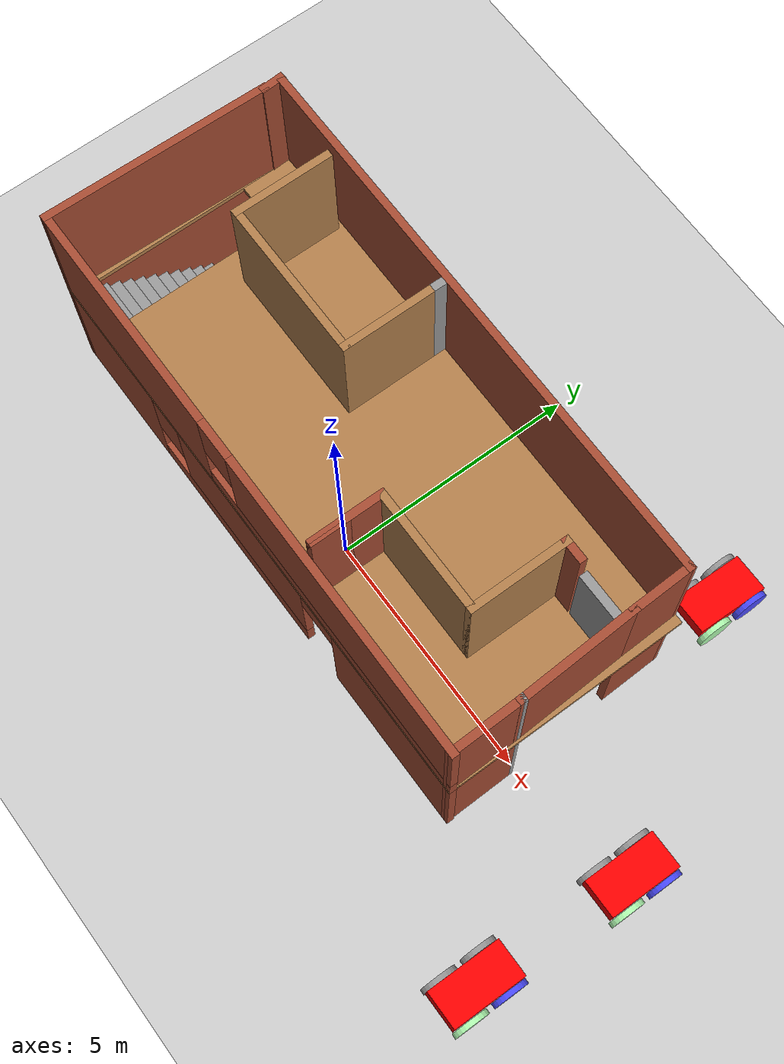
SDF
<sdf version="1.6">
 <world name="default">
  <light name="sun" type="directional">
   <pose>0 0 10 0 -0 0</pose>
   <diffuse>0.8 0.8 0.8 1</diffuse>
   <specular>0.2 0.2 0.2 1</specular>
   <attenuation>
    <range>1000</range>
    <constant>0.9</constant>
    <linear>0.01</linear>
    <quadratic>0.001</quadratic>
   </attenuation>
   <direction>-0.5 0.1 -0.9</direction>
  </light>
  <model name="ground_plane">
   <static>1</static>
   <link name="link">
    <collision name="collision">
     <geometry><plane><normal>0 0 1</normal><size>100 100</size></plane></geometry>
     <surface><friction><ode><mu>100</mu><mu2>50</mu2></ode></friction></surface>
    </collision>
    <visual name="visual">
     <cast_shadows>0</cast_shadows>
     <geometry><plane><normal>0 0 1</normal><size>100 100</size></plane></geometry>
     <material>
      <script><uri>file://media/materials/scripts/gazebo.material</uri><name>Gazebo/Grey</name></script>
     </material>
    </visual>
   </link>
  </model>
  <gravity>0 0 -9.8</gravity>
  <magnetic_field>6e-06 2.3e-05 -4.2e-05</magnetic_field>
  <atmosphere type="adiabatic"/>
  <physics name="default_physics" default="0" type="ode">
   <max_step_size>0.001</max_step_size>
   <real_time_factor>1</real_time_factor>
   <real_time_update_rate>1000</real_time_update_rate>
  </physics>
  <scene><ambient>0.4 0.4 0.4 1</ambient><background>0.7 0.7 0.7 1</background><shadows>1</shadows></scene>
  <spherical_coordinates>
   <surface_model>EARTH_WGS84</surface_model>
   <latitude_deg>0</latitude_deg>
   <longitude_deg>0</longitude_deg>
   <elevation>0</elevation>
   <heading_deg>0</heading_deg>
  </spherical_coordinates>
  <model name="My_garage2">
   <pose>-0.5451 0.88791 0 0 -0 0</pose>
   <link name="Door_0">
    <collision name="Door_0_Collision">
     <geometry><box><size>0.9 0.17 2</size></box></geometry>
     <pose>0 0 1 0 -0 0</pose>
    </collision>
    <visual name="Door_0_Visual">
     <pose>0 0 1 0 -0 0</pose>
     <geometry><box><size>0.9 0.17 2</size></box></geometry>
     <material>
      <script><uri>file://media/materials/scripts/gazebo.material</uri><name>Gazebo/Grey</name></script>
     </material>
    </visual>
    <pose>4.94982 1.09681 2.5 0 -0 0</pose>
   </link>
   <link name="Floor_0">
    <pose>0 -0 2.5 0 -0 0</pose>
    <visual name="Floor_0_Visual_0">
     <pose>-5.62992 0 0.05 0 -0 0</pose>
     <geometry><box><size>0.241489 4.87682 0.1</size></box></geometry>
     <material>
      <script><uri>file://media/materials/scripts/gazebo.material</uri><name>Gazebo/Wood</name></script>
      <ambient>1 1 1 1</ambient>
     </material>
     <meta><layer>1</layer></meta>
    </visual>
    <collision name="Floor_0_Collision_0">
     <geometry><box><size>0.241489 4.87682 0.1</size></box></geometry>
     <pose>-5.62992 0 0.05 0 -0 0</pose>
    </collision>
    <visual name="Floor_0_Visual_1">
     <pose>0.120744 -2.3393 0.05 0 -0 0</pose>
     <geometry><box><size>11.2598 0.198217 0.1</size></box></geometry>
     <material>
      <script><uri>file://media/materials/scripts/gazebo.material</uri><name>Gazebo/Wood</name></script>
      <ambient>1 1 1 1</ambient>
     </material>
     <meta><layer>1</layer></meta>
    </visual>
    <collision name="Floor_0_Collision_1">
     <geometry><box><size>11.2598 0.198217 0.1</size></box></geometry>
     <pose>0.120744 -2.3393 0.05 0 -0 0</pose>
    </collision>
    <visual name="Floor_0_Visual_2">
     <pose>0.620744 0.099108 0.05 0 -0 0</pose>
     <geometry><box><size>10.2598 4.67861 0.1</size></box></geometry>
     <material>
      <script><uri>file://media/materials/scripts/gazebo.material</uri><name>Gazebo/Wood</name></script>
      <ambient>1 1 1 1</ambient>
     </material>
     <meta><layer>1</layer></meta>
    </visual>
    <collision name="Floor_0_Collision_2">
     <geometry><box><size>10.2598 4.67861 0.1</size></box></geometry>
     <pose>0.620744 0.099108 0.05 0 -0 0</pose>
    </collision>
    <visual name="Floor_0_Visual_3">
     <pose>-5.00917 1.84911 0.05 0 -0 0</pose>
     <geometry><box><size>1 1.1786 0.1</size></box></geometry>
     <material>
      <script><uri>file://media/materials/scripts/gazebo.material</uri><name>Gazebo/Wood</name></script>
      <ambient>1 1 1 1</ambient>
     </material>
     <meta><layer>1</layer></meta>
    </visual>
    <collision name="Floor_0_Collision_3">
     <geometry><box><size>1 1.1786 0.1</size></box></geometry>
     <pose>-5.00917 1.84911 0.05 0 -0 0</pose>
    </collision>
   </link>
   <link name="Stairs_0">
    <visual name="Stairs_0_Visual_0">
     <pose>-5.00917 1.14314 0.083333 0 -0 0</pose>
     <geometry><box><size>1 0.233333 0.166667</size></box></geometry>
     <material>
      <script><uri>file://media/materials/scripts/gazebo.material</uri><name>Gazebo/Grey</name></script>
      <ambient>1 1 1 1</ambient>
     </material>
     <meta><layer>0</layer></meta>
    </visual>
    <collision name="Stairs_0_Collision_0">
     <geometry><box><size>1 0.233333 0.166667</size></box></geometry>
     <pose>-5.00917 1.14314 0.083333 0 -0 0</pose>
    </collision>
    <visual name="Stairs_0_Visual_1">
     <pose>-5.00917 0.909806 0.25 0 -0 0</pose>
     <geometry><box><size>1 0.233333 0.166667</size></box></geometry>
     <material>
      <script><uri>file://media/materials/scripts/gazebo.material</uri><name>Gazebo/Grey</name></script>
      <ambient>1 1 1 1</ambient>
     </material>
     <meta><layer>0</layer></meta>
    </visual>
    <collision name="Stairs_0_Collision_1">
     <geometry><box><size>1 0.233333 0.166667</size></box></geometry>
     <pose>-5.00917 0.909806 0.25 0 -0 0</pose>
    </collision>
    <visual name="Stairs_0_Visual_2">
     <pose>-5.00917 0.676473 0.416667 0 -0 0</pose>
     <geometry><box><size>1 0.233333 0.166667</size></box></geometry>
     <material>
      <script><uri>file://media/materials/scripts/gazebo.material</uri><name>Gazebo/Grey</name></script>
      <ambient>1 1 1 1</ambient>
     </material>
     <meta><layer>0</layer></meta>
    </visual>
    <collision name="Stairs_0_Collision_2">
     <geometry><box><size>1 0.233333 0.166667</size></box></geometry>
     <pose>-5.00917 0.676473 0.416667 0 -0 0</pose>
    </collision>
    <visual name="Stairs_0_Visual_3">
     <pose>-5.00917 0.443139 0.583333 0 -0 0</pose>
     <geometry><box><size>1 0.233333 0.166667</size></box></geometry>
     <material>
      <script><uri>file://media/materials/scripts/gazebo.material</uri><name>Gazebo/Grey</name></script>
      <ambient>1 1 1 1</ambient>
     </material>
     <meta><layer>0</layer></meta>
    </visual>
    <collision name="Stairs_0_Collision_3">
     <geometry><box><size>1 0.233333 0.166667</size></box></geometry>
     <pose>-5.00917 0.443139 0.583333 0 -0 0</pose>
    </collision>
    <visual name="Stairs_0_Visual_4">
     <pose>-5.00917 0.209806 0.75 0 -0 0</pose>
     <geometry><box><size>1 0.233333 0.166667</size></box></geometry>
     <material>
      <script><uri>file://media/materials/scripts/gazebo.material</uri><name>Gazebo/Grey</name></script>
      <ambient>1 1 1 1</ambient>
     </material>
     <meta><layer>0</layer></meta>
    </visual>
    <collision name="Stairs_0_Collision_4">
     <geometry><box><size>1 0.233333 0.166667</size></box></geometry>
     <pose>-5.00917 0.209806 0.75 0 -0 0</pose>
    </collision>
    <visual name="Stairs_0_Visual_5">
     <pose>-5.00917 -0.023527 0.916667 0 -0 0</pose>
     <geometry><box><size>1 0.233333 0.166667</size></box></geometry>
     <material>
      <script><uri>file://media/materials/scripts/gazebo.material</uri><name>Gazebo/Grey</name></script>
      <ambient>1 1 1 1</ambient>
     </material>
     <meta><layer>0</layer></meta>
    </visual>
    <collision name="Stairs_0_Collision_5">
     <geometry><box><size>1 0.233333 0.166667</size></box></geometry>
     <pose>-5.00917 -0.023527 0.916667 0 -0 0</pose>
    </collision>
    <visual name="Stairs_0_Visual_6">
     <pose>-5.00917 -0.256861 1.08333 0 -0 0</pose>
     <geometry><box><size>1 0.233333 0.166667</size></box></geometry>
     <material>
      <script><uri>file://media/materials/scripts/gazebo.material</uri><name>Gazebo/Grey</name></script>
      <ambient>1 1 1 1</ambient>
     </material>
     <meta><layer>0</layer></meta>
    </visual>
    <collision name="Stairs_0_Collision_6">
     <geometry><box><size>1 0.233333 0.166667</size></box></geometry>
     <pose>-5.00917 -0.256861 1.08333 0 -0 0</pose>
    </collision>
    <visual name="Stairs_0_Visual_7">
     <pose>-5.00917 -0.490194 1.25 0 -0 0</pose>
     <geometry><box><size>1 0.233333 0.166667</size></box></geometry>
     <material>
      <script><uri>file://media/materials/scripts/gazebo.material</uri><name>Gazebo/Grey</name></script>
      <ambient>1 1 1 1</ambient>
     </material>
     <meta><layer>0</layer></meta>
    </visual>
    <collision name="Stairs_0_Collision_7">
     <geometry><box><size>1 0.233333 0.166667</size></box></geometry>
     <pose>-5.00917 -0.490194 1.25 0 -0 0</pose>
    </collision>
    <visual name="Stairs_0_Visual_8">
     <pose>-5.00917 -0.723527 1.41667 0 -0 0</pose>
     <geometry><box><size>1 0.233333 0.166667</size></box></geometry>
     <material>
      <script><uri>file://media/materials/scripts/gazebo.material</uri><name>Gazebo/Grey</name></script>
      <ambient>1 1 1 1</ambient>
     </material>
     <meta><layer>0</layer></meta>
    </visual>
    <collision name="Stairs_0_Collision_8">
     <geometry><box><size>1 0.233333 0.166667</size></box></geometry>
     <pose>-5.00917 -0.723527 1.41667 0 -0 0</pose>
    </collision>
    <visual name="Stairs_0_Visual_9">
     <pose>-5.00917 -0.956861 1.58333 0 -0 0</pose>
     <geometry><box><size>1 0.233333 0.166667</size></box></geometry>
     <material>
      <script><uri>file://media/materials/scripts/gazebo.material</uri><name>Gazebo/Grey</name></script>
      <ambient>1 1 1 1</ambient>
     </material>
     <meta><layer>0</layer></meta>
    </visual>
    <collision name="Stairs_0_Collision_9">
     <geometry><box><size>1 0.233333 0.166667</size></box></geometry>
     <pose>-5.00917 -0.956861 1.58333 0 -0 0</pose>
    </collision>
    <visual name="Stairs_0_Visual_10">
     <pose>-5.00917 -1.19019 1.75 0 -0 0</pose>
     <geometry><box><size>1 0.233333 0.166667</size></box></geometry>
     <material>
      <script><uri>file://media/materials/scripts/gazebo.material</uri><name>Gazebo/Grey</name></script>
      <ambient>1 1 1 1</ambient>
     </material>
     <meta><layer>0</layer></meta>
    </visual>
    <collision name="Stairs_0_Collision_10">
     <geometry><box><size>1 0.233333 0.166667</size></box></geometry>
     <pose>-5.00917 -1.19019 1.75 0 -0 0</pose>
    </collision>
    <visual name="Stairs_0_Visual_11">
     <pose>-5.00917 -1.42353 1.91667 0 -0 0</pose>
     <geometry><box><size>1 0.233333 0.166667</size></box></geometry>
     <material>
      <script><uri>file://media/materials/scripts/gazebo.material</uri><name>Gazebo/Grey</name></script>
      <ambient>1 1 1 1</ambient>
     </material>
     <meta><layer>0</layer></meta>
    </visual>
    <collision name="Stairs_0_Collision_11">
     <geometry><box><size>1 0.233333 0.166667</size></box></geometry>
     <pose>-5.00917 -1.42353 1.91667 0 -0 0</pose>
    </collision>
    <visual name="Stairs_0_Visual_12">
     <pose>-5.00917 -1.65686 2.08333 0 -0 0</pose>
     <geometry><box><size>1 0.233333 0.166667</size></box></geometry>
     <material>
      <script><uri>file://media/materials/scripts/gazebo.material</uri><name>Gazebo/Grey</name></script>
      <ambient>1 1 1 1</ambient>
     </material>
     <meta><layer>0</layer></meta>
    </visual>
    <collision name="Stairs_0_Collision_12">
     <geometry><box><size>1 0.233333 0.166667</size></box></geometry>
     <pose>-5.00917 -1.65686 2.08333 0 -0 0</pose>
    </collision>
    <visual name="Stairs_0_Visual_13">
     <pose>-5.00917 -1.89019 2.25 0 -0 0</pose>
     <geometry><box><size>1 0.233333 0.166667</size></box></geometry>
     <material>
      <script><uri>file://media/materials/scripts/gazebo.material</uri><name>Gazebo/Grey</name></script>
      <ambient>1 1 1 1</ambient>
     </material>
     <meta><layer>0</layer></meta>
    </visual>
    <collision name="Stairs_0_Collision_13">
     <geometry><box><size>1 0.233333 0.166667</size></box></geometry>
     <pose>-5.00917 -1.89019 2.25 0 -0 0</pose>
    </collision>
    <visual name="Stairs_0_Visual_14">
     <pose>-5.00917 -2.12353 2.41667 0 -0 0</pose>
     <geometry><box><size>1 0.233333 0.166667</size></box></geometry>
     <material>
      <script><uri>file://media/materials/scripts/gazebo.material</uri><name>Gazebo/Grey</name></script>
      <ambient>1 1 1 1</ambient>
     </material>
     <meta><layer>0</layer></meta>
    </visual>
    <collision name="Stairs_0_Collision_14">
     <geometry><box><size>1 0.233333 0.166667</size></box></geometry>
     <pose>-5.00917 -2.12353 2.41667 0 -0 0</pose>
    </collision>
   </link>
   <link name="Wall_0">
    <collision name="Wall_0_Collision">
     <geometry><box><size>4.52115 0.15 2.5</size></box></geometry>
     <pose>0 0 1.25 0 -0 0</pose>
    </collision>
    <visual name="Wall_0_Visual">
     <pose>0 0 1.25 0 -0 0</pose>
     <geometry><box><size>4.52115 0.15 2.5</size></box></geometry>
     <material>
      <script><uri>file://media/materials/scripts/gazebo.material</uri><name>Gazebo/Bricks</name></script>
      <ambient>1 1 1 1</ambient>
     </material>
     <meta><layer>0</layer></meta>
    </visual>
    <pose>-5.63531 -0.176715 0 0 -0 -1.58865</pose>
   </link>
   <link name="Wall_1">
    <pose>0.012164 -2.36208 0 0 -0 0</pose>
    <visual name="Wall_1_Visual_0">
     <pose>-4.38392 0 1.25 0 -0 0</pose>
     <geometry><box><size>2.70916 0.15 2.5</size></box></geometry>
     <material>
      <script><uri>file://media/materials/scripts/gazebo.material</uri><name>Gazebo/Bricks</name></script>
      <ambient>1 1 1 1</ambient>
     </material>
     <meta><layer>0</layer></meta>
    </visual>
    <collision name="Wall_1_Collision_0">
     <geometry><box><size>2.70916 0.15 2.5</size></box></geometry>
     <pose>-4.38392 0 1.25 0 -0 0</pose>
    </collision>
    <visual name="Wall_1_Visual_1">
     <pose>4.07958 0 1.25 0 -0 0</pose>
     <geometry><box><size>3.31784 0.15 2.5</size></box></geometry>
     <material>
      <script><uri>file://media/materials/scripts/gazebo.material</uri><name>Gazebo/Bricks</name></script>
      <ambient>1 1 1 1</ambient>
     </material>
     <meta><layer>0</layer></meta>
    </visual>
    <collision name="Wall_1_Collision_1">
     <geometry><box><size>3.31784 0.15 2.5</size></box></geometry>
     <pose>4.07958 0 1.25 0 -0 0</pose>
    </collision>
    <visual name="Wall_1_Visual_2">
     <pose>-0.754338 0 0.25 0 -0 0</pose>
     <geometry><box><size>4.55 0.15 0.5</size></box></geometry>
     <material>
      <script><uri>file://media/materials/scripts/gazebo.material</uri><name>Gazebo/Bricks</name></script>
      <ambient>1 1 1 1</ambient>
     </material>
     <meta><layer>0</layer></meta>
    </visual>
    <collision name="Wall_1_Collision_2">
     <geometry><box><size>4.55 0.15 0.5</size></box></geometry>
     <pose>-0.754338 0 0.25 0 -0 0</pose>
    </collision>
    <visual name="Wall_1_Visual_3">
     <pose>-0.354338 0 1.5 0 -0 0</pose>
     <geometry><box><size>3.75 0.15 2</size></box></geometry>
     <material>
      <script><uri>file://media/materials/scripts/gazebo.material</uri><name>Gazebo/Bricks</name></script>
      <ambient>1 1 1 1</ambient>
     </material>
     <meta><layer>0</layer></meta>
    </visual>
    <collision name="Wall_1_Collision_3">
     <geometry><box><size>3.75 0.15 2</size></box></geometry>
     <pose>-0.354338 0 1.5 0 -0 0</pose>
    </collision>
    <visual name="Wall_1_Visual_4">
     <pose>-2.62934 0 1.9 0 -0 0</pose>
     <geometry><box><size>0.8 0.15 1.2</size></box></geometry>
     <material>
      <script><uri>file://media/materials/scripts/gazebo.material</uri><name>Gazebo/Bricks</name></script>
      <ambient>1 1 1 1</ambient>
     </material>
     <meta><layer>0</layer></meta>
    </visual>
    <collision name="Wall_1_Collision_4">
     <geometry><box><size>0.8 0.15 1.2</size></box></geometry>
     <pose>-2.62934 0 1.9 0 -0 0</pose>
    </collision>
    <visual name="Wall_1_Visual_5">
     <pose>1.97066 0 2.25 0 -0 0</pose>
     <geometry><box><size>0.9 0.15 0.5</size></box></geometry>
     <material>
      <script><uri>file://media/materials/scripts/gazebo.material</uri><name>Gazebo/Bricks</name></script>
      <ambient>1 1 1 1</ambient>
     </material>
     <meta><layer>0</layer></meta>
    </visual>
    <collision name="Wall_1_Collision_5">
     <geometry><box><size>0.9 0.15 0.5</size></box></geometry>
     <pose>1.97066 0 2.25 0 -0 0</pose>
    </collision>
   </link>
   <link name="Wall_11">
    <collision name="Wall_11_Collision">
     <geometry><box><size>4.52143 0.15 2.5</size></box></geometry>
     <pose>0 0 1.25 0 -0 0</pose>
    </collision>
    <visual name="Wall_11_Visual">
     <pose>0 0 1.25 0 -0 0</pose>
     <geometry><box><size>4.52143 0.15 2.5</size></box></geometry>
     <material>
      <script><uri>file://media/materials/scripts/gazebo.material</uri><name>Gazebo/Bricks</name></script>
      <ambient>1 1 1 1</ambient>
     </material>
     <meta><layer>1</layer></meta>
    </visual>
    <pose>-5.63531 -0.176715 2.5 0 -0 -1.58865</pose>
   </link>
   <link name="Wall_12">
    <pose>0.012164 -2.36208 2.5 0 -0 0</pose>
    <visual name="Wall_12_Visual_0">
     <pose>-3.40642 0 1.25 0 -0 0</pose>
     <geometry><box><size>4.66416 0.15 2.5</size></box></geometry>
     <material>
      <script><uri>file://media/materials/scripts/gazebo.material</uri><name>Gazebo/Bricks</name></script>
      <ambient>1 1 1 1</ambient>
     </material>
     <meta><layer>1</layer></meta>
    </visual>
    <collision name="Wall_12_Collision_0">
     <geometry><box><size>4.66416 0.15 2.5</size></box></geometry>
     <pose>-3.40642 0 1.25 0 -0 0</pose>
    </collision>
    <visual name="Wall_12_Visual_1">
     <pose>2.33208 0 0.25 0 -0 0</pose>
     <geometry><box><size>6.81284 0.15 0.5</size></box></geometry>
     <material>
      <script><uri>file://media/materials/scripts/gazebo.material</uri><name>Gazebo/Bricks</name></script>
      <ambient>1 1 1 1</ambient>
     </material>
     <meta><layer>1</layer></meta>
    </visual>
    <collision name="Wall_12_Collision_1">
     <geometry><box><size>6.81284 0.15 0.5</size></box></geometry>
     <pose>2.33208 0 0.25 0 -0 0</pose>
    </collision>
    <visual name="Wall_12_Visual_2">
     <pose>2.73208 0 1.5 0 -0 0</pose>
     <geometry><box><size>6.01284 0.15 2</size></box></geometry>
     <material>
      <script><uri>file://media/materials/scripts/gazebo.material</uri><name>Gazebo/Bricks</name></script>
      <ambient>1 1 1 1</ambient>
     </material>
     <meta><layer>1</layer></meta>
    </visual>
    <collision name="Wall_12_Collision_2">
     <geometry><box><size>6.01284 0.15 2</size></box></geometry>
     <pose>2.73208 0 1.5 0 -0 0</pose>
    </collision>
    <visual name="Wall_12_Visual_3">
     <pose>-0.674338 0 1.9 0 -0 0</pose>
     <geometry><box><size>0.8 0.15 1.2</size></box></geometry>
     <material>
      <script><uri>file://media/materials/scripts/gazebo.material</uri><name>Gazebo/Bricks</name></script>
      <ambient>1 1 1 1</ambient>
     </material>
     <meta><layer>1</layer></meta>
    </visual>
    <collision name="Wall_12_Collision_3">
     <geometry><box><size>0.8 0.15 1.2</size></box></geometry>
     <pose>-0.674338 0 1.9 0 -0 0</pose>
    </collision>
   </link>
   <link name="Wall_13">
    <collision name="Wall_13_Collision">
     <geometry><box><size>1.4772 0.15 2.5</size></box></geometry>
     <pose>0 0 1.25 0 -0 0</pose>
    </collision>
    <visual name="Wall_13_Visual">
     <pose>0 0 1.25 0 -0 0</pose>
     <geometry><box><size>1.4772 0.15 2.5</size></box></geometry>
     <material>
      <script><uri>file://media/materials/scripts/gazebo.material</uri><name>Gazebo/Bricks</name></script>
      <ambient>1 1 1 1</ambient>
     </material>
     <meta><layer>1</layer></meta>
    </visual>
    <pose>5.64116 -1.69858 2.5 0 -0 1.58813</pose>
   </link>
   <link name="Wall_14">
    <collision name="Wall_14_Collision">
     <geometry><box><size>0.15 0.15 2.5</size></box></geometry>
     <pose>0 0 1.25 0 -0 0</pose>
    </collision>
    <visual name="Wall_14_Visual">
     <pose>0 0 1.25 0 -0 0</pose>
     <geometry><box><size>0.15 0.15 2.5</size></box></geometry>
     <material>
      <script><uri>file://media/materials/scripts/gazebo.material</uri><name>Gazebo/Grey</name></script>
      <ambient>1 1 1 1</ambient>
     </material>
     <meta><layer>1</layer></meta>
    </visual>
    <pose>5.62966 -1.03508 2.5 0 -0 0</pose>
   </link>
   <link name="Wall_15">
    <collision name="Wall_15_Collision">
     <geometry><box><size>1.28083 0.15 2.5</size></box></geometry>
     <pose>0 0 1.25 0 -0 0</pose>
    </collision>
    <visual name="Wall_15_Visual">
     <pose>0 0 1.25 0 -0 0</pose>
     <geometry><box><size>1.28083 0.15 2.5</size></box></geometry>
     <material>
      <script><uri>file://media/materials/scripts/gazebo.material</uri><name>Gazebo/Bricks</name></script>
      <ambient>1 1 1 1</ambient>
     </material>
     <meta><layer>1</layer></meta>
    </visual>
    <pose>5.51893 1.79344 2.5 0 -0 1.5977</pose>
   </link>
   <link name="Wall_16">
    <collision name="Wall_16_Collision">
     <geometry><box><size>11.1892 0.15 2.5</size></box></geometry>
     <pose>0 0 1.25 0 -0 0</pose>
    </collision>
    <visual name="Wall_16_Visual">
     <pose>0 0 1.25 0 -0 0</pose>
     <geometry><box><size>11.1892 0.15 2.5</size></box></geometry>
     <material>
      <script><uri>file://media/materials/scripts/gazebo.material</uri><name>Gazebo/Bricks</name></script>
      <ambient>1 1 1 1</ambient>
     </material>
     <meta><layer>1</layer></meta>
    </visual>
    <pose>-0.015861 2.35865 2.5 0 -0 3.14159</pose>
   </link>
   <link name="Wall_17">
    <collision name="Wall_17_Collision">
     <geometry><box><size>0.500755 0.15 2.5</size></box></geometry>
     <pose>0 0 1.25 0 -0 0</pose>
    </collision>
    <visual name="Wall_17_Visual">
     <pose>0 0 1.25 0 -0 0</pose>
     <geometry><box><size>0.500755 0.15 2.5</size></box></geometry>
     <material>
      <script><uri>file://media/materials/scripts/gazebo.material</uri><name>Gazebo/Bricks</name></script>
      <ambient>1 1 1 1</ambient>
     </material>
     <meta><layer>1</layer></meta>
    </visual>
    <pose>-5.58478 2.18365 2.5 0 -0 -1.50518</pose>
   </link>
   <link name="Wall_18">
    <collision name="Wall_18_Collision">
     <geometry><box><size>2 0.15 2.5</size></box></geometry>
     <pose>0 0 1.25 0 -0 0</pose>
    </collision>
    <visual name="Wall_18_Visual">
     <pose>0 0 1.25 0 -0 0</pose>
     <geometry><box><size>2 0.15 2.5</size></box></geometry>
     <material>
      <script><uri>file://media/materials/scripts/gazebo.material</uri><name>Gazebo/Wood</name></script>
      <ambient>1 1 1 1</ambient>
     </material>
     <meta><layer>1</layer></meta>
    </visual>
    <pose>-3.85918 1.18381 2.5 0 -0 -1.5708</pose>
   </link>
   <link name="Wall_19">
    <collision name="Wall_19_Collision">
     <geometry><box><size>3.25 0.15 2.5</size></box></geometry>
     <pose>0 0 1.25 0 -0 0</pose>
    </collision>
    <visual name="Wall_19_Visual">
     <pose>0 0 1.25 0 -0 0</pose>
     <geometry><box><size>3.25 0.15 2.5</size></box></geometry>
     <material>
      <script><uri>file://media/materials/scripts/gazebo.material</uri><name>Gazebo/Wood</name></script>
      <ambient>1 1 1 1</ambient>
     </material>
     <meta><layer>1</layer></meta>
    </visual>
    <pose>-2.30918 0.258806 2.5 0 -0 0</pose>
   </link>
   <link name="Wall_2">
    <collision name="Wall_2_Collision">
     <geometry><box><size>1.4772 0.15 2.5</size></box></geometry>
     <pose>0 0 1.25 0 -0 0</pose>
    </collision>
    <visual name="Wall_2_Visual">
     <pose>0 0 1.25 0 -0 0</pose>
     <geometry><box><size>1.4772 0.15 2.5</size></box></geometry>
     <material>
      <script><uri>file://media/materials/scripts/gazebo.material</uri><name>Gazebo/Bricks</name></script>
      <ambient>1 1 1 1</ambient>
     </material>
     <meta><layer>0</layer></meta>
    </visual>
    <pose>5.64116 -1.69858 0 0 -0 1.58813</pose>
   </link>
   <link name="Wall_20">
    <collision name="Wall_20_Collision">
     <geometry><box><size>2 0.15 2.5</size></box></geometry>
     <pose>0 0 1.25 0 -0 0</pose>
    </collision>
    <visual name="Wall_20_Visual">
     <pose>0 0 1.25 0 -0 0</pose>
     <geometry><box><size>2 0.15 2.5</size></box></geometry>
     <material>
      <script><uri>file://media/materials/scripts/gazebo.material</uri><name>Gazebo/Wood</name></script>
      <ambient>1 1 1 1</ambient>
     </material>
     <meta><layer>1</layer></meta>
    </visual>
    <pose>-0.759174 1.18381 2.5 0 -0 1.5708</pose>
   </link>
   <link name="Wall_21">
    <collision name="Wall_21_Collision">
     <geometry><box><size>0.25 0.15 2.5</size></box></geometry>
     <pose>0 0 1.25 0 -0 0</pose>
    </collision>
    <visual name="Wall_21_Visual">
     <pose>0 0 1.25 0 -0 0</pose>
     <geometry><box><size>0.25 0.15 2.5</size></box></geometry>
     <material>
      <script><uri>file://media/materials/scripts/gazebo.material</uri><name>Gazebo/Grey</name></script>
      <ambient>1 1 1 1</ambient>
     </material>
     <meta><layer>1</layer></meta>
    </visual>
    <pose>-0.759174 2.15881 2.5 0 -0 1.5708</pose>
   </link>
   <link name="Wall_23">
    <collision name="Wall_23_Collision">
     <geometry><box><size>1.5 0.15 2.5</size></box></geometry>
     <pose>0 0 1.25 0 -0 0</pose>
    </collision>
    <visual name="Wall_23_Visual">
     <pose>0 0 1.25 0 -0 0</pose>
     <geometry><box><size>1.5 0.15 2.5</size></box></geometry>
     <material>
      <script><uri>file://media/materials/scripts/gazebo.material</uri><name>Gazebo/Bricks</name></script>
      <ambient>1 1 1 1</ambient>
     </material>
     <meta><layer>1</layer></meta>
    </visual>
    <pose>1.68382 -1.44119 2.5 0 -0 -1.5708</pose>
   </link>
   <link name="Wall_24">
    <collision name="Wall_24_Collision">
     <geometry><box><size>1.5 0.15 2.5</size></box></geometry>
     <pose>0 0 1.25 0 -0 0</pose>
    </collision>
    <visual name="Wall_24_Visual">
     <pose>0 0 1.25 0 -0 0</pose>
     <geometry><box><size>1.5 0.15 2.5</size></box></geometry>
     <material>
      <script><uri>file://media/materials/scripts/gazebo.material</uri><name>Gazebo/Bricks</name></script>
      <ambient>1 1 1 1</ambient>
     </material>
     <meta><layer>1</layer></meta>
    </visual>
    <pose>1.68382 -1.44119 2.5 0 -0 1.5708</pose>
   </link>
   <link name="Wall_25">
    <collision name="Wall_25_Collision">
     <geometry><box><size>2.5 0.15 2.5</size></box></geometry>
     <pose>0 0 1.25 0 -0 0</pose>
    </collision>
    <visual name="Wall_25_Visual">
     <pose>0 0 1.25 0 -0 0</pose>
     <geometry><box><size>2.5 0.15 2.5</size></box></geometry>
     <material>
      <script><uri>file://media/materials/scripts/gazebo.material</uri><name>Gazebo/Wood</name></script>
      <ambient>1 1 1 1</ambient>
     </material>
     <meta><layer>1</layer></meta>
    </visual>
    <pose>2.85883 -0.766194 2.5 0 -0 0</pose>
   </link>
   <link name="Wall_26">
    <collision name="Wall_26_Collision">
     <geometry><box><size>2 0.15 2.5</size></box></geometry>
     <pose>0 0 1.25 0 -0 0</pose>
    </collision>
    <visual name="Wall_26_Visual">
     <pose>0 0 1.25 0 -0 0</pose>
     <geometry><box><size>2 0.15 2.5</size></box></geometry>
     <material>
      <script><uri>file://media/materials/scripts/gazebo.material</uri><name>Gazebo/Wood</name></script>
      <ambient>1 1 1 1</ambient>
     </material>
     <meta><layer>1</layer></meta>
    </visual>
    <pose>4.03383 0.158806 2.5 0 -0 1.5708</pose>
   </link>
   <link name="Wall_27">
    <collision name="Wall_27_Collision">
     <geometry><box><size>0.5 0.15 2.5</size></box></geometry>
     <pose>0 0 1.25 0 -0 0</pose>
    </collision>
    <visual name="Wall_27_Visual">
     <pose>0 0 1.25 0 -0 0</pose>
     <geometry><box><size>0.5 0.15 2.5</size></box></geometry>
     <material>
      <script><uri>file://media/materials/scripts/gazebo.material</uri><name>Gazebo/Bricks</name></script>
      <ambient>1 1 1 1</ambient>
     </material>
     <meta><layer>1</layer></meta>
    </visual>
    <pose>4.20883 1.08381 2.5 0 -0 0</pose>
   </link>
   <link name="Wall_29">
    <collision name="Wall_29_Collision">
     <geometry><box><size>2.41533 0.15 2.5</size></box></geometry>
     <pose>0 0 1.25 0 -0 0</pose>
    </collision>
    <visual name="Wall_29_Visual">
     <pose>0 0 1.25 0 -0 0</pose>
     <geometry><box><size>2.41533 0.15 2.5</size></box></geometry>
     <material>
      <script><uri>file://media/materials/scripts/gazebo.material</uri><name>Gazebo/Bricks</name></script>
      <ambient>1 1 1 1</ambient>
     </material>
     <meta><layer>1</layer></meta>
    </visual>
    <pose>5.5819 0.096577 2.5 0 -0 -1.52862</pose>
   </link>
   <link name="Wall_3">
    <collision name="Wall_3_Collision">
     <geometry><box><size>0.15 0.15 2.5</size></box></geometry>
     <pose>0 0 1.25 0 -0 0</pose>
    </collision>
    <visual name="Wall_3_Visual">
     <pose>0 0 1.25 0 -0 0</pose>
     <geometry><box><size>0.15 0.15 2.5</size></box></geometry>
     <material>
      <script><uri>file://media/materials/scripts/gazebo.material</uri><name>Gazebo/Grey</name></script>
      <ambient>1 1 1 1</ambient>
     </material>
     <meta><layer>0</layer></meta>
    </visual>
    <pose>5.62966 -1.03508 0 0 -0 0</pose>
   </link>
   <link name="Wall_5">
    <collision name="Wall_5_Collision">
     <geometry><box><size>1.28083 0.15 2.5</size></box></geometry>
     <pose>0 0 1.25 0 -0 0</pose>
    </collision>
    <visual name="Wall_5_Visual">
     <pose>0 0 1.25 0 -0 0</pose>
     <geometry><box><size>1.28083 0.15 2.5</size></box></geometry>
     <material>
      <script><uri>file://media/materials/scripts/gazebo.material</uri><name>Gazebo/Bricks</name></script>
      <ambient>1 1 1 1</ambient>
     </material>
     <meta><layer>0</layer></meta>
    </visual>
    <pose>5.51893 1.79344 0 0 -0 1.5977</pose>
   </link>
   <link name="Wall_8">
    <collision name="Wall_8_Collision">
     <geometry><box><size>11.1892 0.15 2.5</size></box></geometry>
     <pose>0 0 1.25 0 -0 0</pose>
    </collision>
    <visual name="Wall_8_Visual">
     <pose>0 0 1.25 0 -0 0</pose>
     <geometry><box><size>11.1892 0.15 2.5</size></box></geometry>
     <material>
      <script><uri>file://media/materials/scripts/gazebo.material</uri><name>Gazebo/Bricks</name></script>
      <ambient>1 1 1 1</ambient>
     </material>
     <meta><layer>0</layer></meta>
    </visual>
    <pose>-0.015861 2.35865 0 0 -0 3.14159</pose>
   </link>
   <link name="Wall_9">
    <collision name="Wall_9_Collision">
     <geometry><box><size>0.500755 0.15 2.5</size></box></geometry>
     <pose>0 0 1.25 0 -0 0</pose>
    </collision>
    <visual name="Wall_9_Visual">
     <pose>0 0 1.25 0 -0 0</pose>
     <geometry><box><size>0.500755 0.15 2.5</size></box></geometry>
     <material>
      <script><uri>file://media/materials/scripts/gazebo.material</uri><name>Gazebo/Bricks</name></script>
      <ambient>1 1 1 1</ambient>
     </material>
     <meta><layer>0</layer></meta>
    </visual>
    <pose>-5.58478 2.18365 0 0 -0 -1.50518</pose>
   </link>
   <static>1</static>
  </model>
  <model name="my_car2">
   <link name="link_0">
    <inertial>
     <mass>0.276053</mass>
     <inertia>
      <ixx>0.0553179</ixx>
      <ixy>0</ixy>
      <ixz>0</ixz>
      <iyy>0.0149267</iyy>
      <iyz>0</iyz>
      <izz>0.0677343</izz>
     </inertia>
    </inertial>
    <pose>0.341303 -0.303641 0.194258 0 -0 0</pose>
    <visual name="visual">
     <geometry><box><size>0.770868 1.533 0.233602</size></box></geometry>
     <material>
      <lighting>1</lighting>
      <script><uri>file://media/materials/scripts/gazebo.material</uri><name>Gazebo/Grey</name></script>
      <emissive>1 0 0 1</emissive>
      <diffuse>1 0 0 0</diffuse>
      <shader type="vertex"><normal_map>__default__</normal_map></shader>
      <ambient>0.3 0.3 0.3 1</ambient>
      <specular>1 0.01 0.01 1</specular>
     </material>
    </visual>
    <collision name="collision">
     <geometry><box><size>0.770868 1.533 0.233602</size></box></geometry>
     <surface>
      <friction>
       <ode><mu>1</mu><mu2>1</mu2><fdir1>0 0 0</fdir1><slip1>0</slip1><slip2>0</slip2></ode>
       <torsional>
        <coefficient>1</coefficient>
        <patch_radius>0</patch_radius>
        <surface_radius>0</surface_radius>
        <use_patch_radius>1</use_patch_radius>
        <ode><slip>0</slip></ode>
       </torsional>
      </friction>
      <bounce><restitution_coefficient>0</restitution_coefficient><threshold>1e+06</threshold></bounce>
      <contact>
       <collide_without_contact>0</collide_without_contact>
       <collide_without_contact_bitmask>1</collide_without_contact_bitmask>
       <collide_bitmask>1</collide_bitmask>
       <ode>
        <soft_cfm>0</soft_cfm>
        <soft_erp>0.2</soft_erp>
        <kp>1e+13</kp>
        <kd>1</kd>
        <max_vel>0.01</max_vel>
        <min_depth>0</min_depth>
       </ode>
       <bullet>
        <split_impulse>1</split_impulse>
        <split_impulse_penetration_threshold>-0.01</split_impulse_penetration_threshold>
        <soft_cfm>0</soft_cfm>
        <soft_erp>0.2</soft_erp>
        <kp>1e+13</kp>
        <kd>1</kd>
       </bullet>
      </contact>
     </surface>
    </collision>
   </link>
   <link name="link_1_clone">
    <inertial>
     <mass>0.0516188</mass>
     <inertia>
      <ixx>0.00169164</ixx>
      <ixy>0</ixy>
      <ixz>0</ixz>
      <iyy>0.00169164</iyy>
      <iyz>0</iyz>
      <izz>0.00329539</izz>
     </inertia>
    </inertial>
    <pose>0.787793 0.105537 0.097767 3.14159 1.54127 3.14159</pose>
    <visual name="visual">
     <geometry><cylinder><radius>0.357323</radius><length>0.101057</length></cylinder></geometry>
     <material>
      <lighting>1</lighting>
      <script><uri>file://media/materials/scripts/gazebo.material</uri><name>Gazebo/Grey</name></script>
      <shader type="vertex"><normal_map>__default__</normal_map></shader>
      <ambient>0.3 0.3 1 1</ambient>
      <diffuse>0.7 0.7 0.7 1</diffuse>
      <specular>0.01 0.01 0.01 1</specular>
      <emissive>0 0 0 1</emissive>
     </material>
    </visual>
    <collision name="collision">
     <geometry><cylinder><radius>0.357323</radius><length>0.101057</length></cylinder></geometry>
     <surface>
      <friction>
       <ode><mu>1</mu><mu2>1</mu2><fdir1>0 0 0</fdir1><slip1>0</slip1><slip2>0</slip2></ode>
       <torsional>
        <coefficient>1</coefficient>
        <patch_radius>0</patch_radius>
        <surface_radius>0</surface_radius>
        <use_patch_radius>1</use_patch_radius>
        <ode><slip>0</slip></ode>
       </torsional>
      </friction>
      <bounce><restitution_coefficient>0</restitution_coefficient><threshold>1e+06</threshold></bounce>
      <contact>
       <collide_without_contact>0</collide_without_contact>
       <collide_without_contact_bitmask>1</collide_without_contact_bitmask>
       <collide_bitmask>1</collide_bitmask>
       <ode>
        <soft_cfm>0</soft_cfm>
        <soft_erp>0.2</soft_erp>
        <kp>1e+13</kp>
        <kd>1</kd>
        <max_vel>0.01</max_vel>
        <min_depth>0</min_depth>
       </ode>
       <bullet>
        <split_impulse>1</split_impulse>
        <split_impulse_penetration_threshold>-0.01</split_impulse_penetration_threshold>
        <soft_cfm>0</soft_cfm>
        <soft_erp>0.2</soft_erp>
        <kp>1e+13</kp>
        <kd>1</kd>
       </bullet>
      </contact>
     </surface>
    </collision>
   </link>
   <link name="link_1_clone_0">
    <inertial>
     <mass>0.0516188</mass>
     <inertia>
      <ixx>0.00169164</ixx>
      <ixy>0</ixy>
      <ixz>0</ixz>
      <iyy>0.00169164</iyy>
      <iyz>0</iyz>
      <izz>0.00329539</izz>
     </inertia>
    </inertial>
    <pose>-0.105186 -0.712819 -0.024401 3.14159 1.54127 3.14159</pose>
    <visual name="visual">
     <geometry><cylinder><radius>0.357323</radius><length>0.101057</length></cylinder></geometry>
     <material>
      <lighting>1</lighting>
      <script><uri>file://media/materials/scripts/gazebo.material</uri><name>Gazebo/Grey</name></script>
      <shader type="vertex"><normal_map>__default__</normal_map></shader>
      <ambient>0.3 0.3 0.3 1</ambient>
      <diffuse>0.7 0.7 0.7 1</diffuse>
      <specular>0.01 0.01 1 1</specular>
      <emissive>0 0 0 1</emissive>
     </material>
    </visual>
    <collision name="collision">
     <geometry><cylinder><radius>0.357323</radius><length>0.101057</length></cylinder></geometry>
     <surface>
      <friction>
       <ode><mu>1</mu><mu2>1</mu2><fdir1>0 0 0</fdir1><slip1>0</slip1><slip2>0</slip2></ode>
       <torsional>
        <coefficient>1</coefficient>
        <patch_radius>0</patch_radius>
        <surface_radius>0</surface_radius>
        <use_patch_radius>1</use_patch_radius>
        <ode><slip>0</slip></ode>
       </torsional>
      </friction>
      <bounce><restitution_coefficient>0</restitution_coefficient><threshold>1e+06</threshold></bounce>
      <contact>
       <collide_without_contact>0</collide_without_contact>
       <collide_without_contact_bitmask>1</collide_without_contact_bitmask>
       <collide_bitmask>1</collide_bitmask>
       <ode>
        <soft_cfm>0</soft_cfm>
        <soft_erp>0.2</soft_erp>
        <kp>1e+13</kp>
        <kd>1</kd>
        <max_vel>0.01</max_vel>
        <min_depth>0</min_depth>
       </ode>
       <bullet>
        <split_impulse>1</split_impulse>
        <split_impulse_penetration_threshold>-0.01</split_impulse_penetration_threshold>
        <soft_cfm>0</soft_cfm>
        <soft_erp>0.2</soft_erp>
        <kp>1e+13</kp>
        <kd>1</kd>
       </bullet>
      </contact>
     </surface>
    </collision>
   </link>
   <link name="link_1_clone_1">
    <inertial>
     <mass>0.0516188</mass>
     <inertia>
      <ixx>0.00169164</ixx>
      <ixy>0</ixy>
      <ixz>0</ixz>
      <iyy>0.00169164</iyy>
      <iyz>0</iyz>
      <izz>0.00329539</izz>
     </inertia>
    </inertial>
    <pose>0.787793 -0.712819 -0.024401 3.14159 1.54127 3.14159</pose>
    <visual name="visual">
     <geometry><cylinder><radius>0.357323</radius><length>0.101057</length></cylinder></geometry>
     <material>
      <lighting>1</lighting>
      <script><uri>file://media/materials/scripts/gazebo.material</uri><name>Gazebo/Grey</name></script>
      <shader type="vertex"><normal_map>__default__</normal_map></shader>
      <ambient>0.3 1 0.3 1</ambient>
      <diffuse>0.7 1 0.7 1</diffuse>
      <specular>0.01 1 0.01 1</specular>
      <emissive>0 1 0 1</emissive>
     </material>
    </visual>
    <collision name="collision">
     <geometry><cylinder><radius>0.357323</radius><length>0.101057</length></cylinder></geometry>
     <surface>
      <friction>
       <ode><mu>1</mu><mu2>1</mu2><fdir1>0 0 0</fdir1><slip1>0</slip1><slip2>0</slip2></ode>
       <torsional>
        <coefficient>1</coefficient>
        <patch_radius>0</patch_radius>
        <surface_radius>0</surface_radius>
        <use_patch_radius>1</use_patch_radius>
        <ode><slip>0</slip></ode>
       </torsional>
      </friction>
      <bounce><restitution_coefficient>0</restitution_coefficient><threshold>1e+06</threshold></bounce>
      <contact>
       <collide_without_contact>0</collide_without_contact>
       <collide_without_contact_bitmask>1</collide_without_contact_bitmask>
       <collide_bitmask>1</collide_bitmask>
       <ode>
        <soft_cfm>0</soft_cfm>
        <soft_erp>0.2</soft_erp>
        <kp>1e+13</kp>
        <kd>1</kd>
        <max_vel>0.01</max_vel>
        <min_depth>0</min_depth>
       </ode>
       <bullet>
        <split_impulse>1</split_impulse>
        <split_impulse_penetration_threshold>-0.01</split_impulse_penetration_threshold>
        <soft_cfm>0</soft_cfm>
        <soft_erp>0.2</soft_erp>
        <kp>1e+13</kp>
        <kd>1</kd>
       </bullet>
      </contact>
     </surface>
    </collision>
   </link>
   <link name="link_1_clone_clone">
    <inertial>
     <mass>0.0516188</mass>
     <inertia>
      <ixx>0.00169164</ixx>
      <ixy>0</ixy>
      <ixz>0</ixz>
      <iyy>0.00169164</iyy>
      <iyz>0</iyz>
      <izz>0.00329539</izz>
     </inertia>
    </inertial>
    <pose>-0.105186 0.105537 0.097767 3.14159 1.54127 3.14159</pose>
    <visual name="visual">
     <geometry><cylinder><radius>0.357323</radius><length>0.101057</length></cylinder></geometry>
     <material>
      <lighting>1</lighting>
      <script><uri>file://media/materials/scripts/gazebo.material</uri><name>Gazebo/Grey</name></script>
      <shader type="vertex"><normal_map>__default__</normal_map></shader>
      <ambient>0.3 0.3 0.3 1</ambient>
      <diffuse>0.7 0.7 0.7 1</diffuse>
      <specular>0.01 1 0.01 1</specular>
      <emissive>0 1 0 1</emissive>
     </material>
    </visual>
    <collision name="collision">
     <geometry><cylinder><radius>0.357323</radius><length>0.101057</length></cylinder></geometry>
     <surface>
      <friction>
       <ode><mu>1</mu><mu2>1</mu2><fdir1>0 0 0</fdir1><slip1>0</slip1><slip2>0</slip2></ode>
       <torsional>
        <coefficient>1</coefficient>
        <patch_radius>0</patch_radius>
        <surface_radius>0</surface_radius>
        <use_patch_radius>1</use_patch_radius>
        <ode><slip>0</slip></ode>
       </torsional>
      </friction>
      <bounce><restitution_coefficient>0</restitution_coefficient><threshold>1e+06</threshold></bounce>
      <contact>
       <collide_without_contact>0</collide_without_contact>
       <collide_without_contact_bitmask>1</collide_without_contact_bitmask>
       <collide_bitmask>1</collide_bitmask>
       <ode>
        <soft_cfm>0</soft_cfm>
        <soft_erp>0.2</soft_erp>
        <kp>1e+13</kp>
        <kd>1</kd>
        <max_vel>0.01</max_vel>
        <min_depth>0</min_depth>
       </ode>
       <bullet>
        <split_impulse>1</split_impulse>
        <split_impulse_penetration_threshold>-0.01</split_impulse_penetration_threshold>
        <soft_cfm>0</soft_cfm>
        <soft_erp>0.2</soft_erp>
        <kp>1e+13</kp>
        <kd>1</kd>
       </bullet>
      </contact>
     </surface>
    </collision>
   </link>
   <joint name="link_0_JOINT_2" type="revolute">
    <parent>link_0</parent>
    <child>link_1_clone_1</child>
    <axis>
     <xyz>0 0 1</xyz>
     <use_parent_model_frame>0</use_parent_model_frame>
     <limit>
      <lower>-1.79769e+308</lower>
      <upper>1.79769e+308</upper>
      <effort>-1</effort>
      <velocity>-1</velocity>
     </limit>
     <dynamics>
      <spring_reference>0</spring_reference>
      <spring_stiffness>0</spring_stiffness>
      <damping>0</damping>
      <friction>0</friction>
     </dynamics>
    </axis>
    <physics>
     <ode><limit><cfm>0</cfm><erp>0.2</erp></limit><suspension><cfm>0</cfm><erp>0.2</erp></suspension></ode>
    </physics>
   </joint>
   <joint name="link_0_JOINT_3" type="revolute">
    <parent>link_0</parent>
    <child>link_1_clone</child>
    <axis>
     <xyz>0 0 1</xyz>
     <use_parent_model_frame>0</use_parent_model_frame>
     <limit>
      <lower>-1.79769e+308</lower>
      <upper>1.79769e+308</upper>
      <effort>-1</effort>
      <velocity>-1</velocity>
     </limit>
     <dynamics>
      <spring_reference>0</spring_reference>
      <spring_stiffness>0</spring_stiffness>
      <damping>0</damping>
      <friction>0</friction>
     </dynamics>
    </axis>
    <physics>
     <ode><limit><cfm>0</cfm><erp>0.2</erp></limit><suspension><cfm>0</cfm><erp>0.2</erp></suspension></ode>
    </physics>
   </joint>
   <joint name="link_0_JOINT_4" type="revolute">
    <parent>link_0</parent>
    <child>link_1_clone_0</child>
    <axis>
     <xyz>0 0 1</xyz>
     <use_parent_model_frame>0</use_parent_model_frame>
     <limit>
      <lower>-1.79769e+308</lower>
      <upper>1.79769e+308</upper>
      <effort>-1</effort>
      <velocity>-1</velocity>
     </limit>
     <dynamics>
      <spring_reference>0</spring_reference>
      <spring_stiffness>0</spring_stiffness>
      <damping>0</damping>
      <friction>0</friction>
     </dynamics>
    </axis>
    <physics>
     <ode><limit><cfm>0</cfm><erp>0.2</erp></limit><suspension><cfm>0</cfm><erp>0.2</erp></suspension></ode>
    </physics>
   </joint>
   <joint name="link_0_JOINT_6" type="revolute">
    <parent>link_0</parent>
    <child>link_1_clone_clone</child>
    <axis>
     <xyz>0 0 1</xyz>
     <use_parent_model_frame>0</use_parent_model_frame>
     <limit>
      <lower>-1.79769e+308</lower>
      <upper>1.79769e+308</upper>
      <effort>-1</effort>
      <velocity>-1</velocity>
     </limit>
     <dynamics>
      <spring_reference>0</spring_reference>
      <spring_stiffness>0</spring_stiffness>
      <damping>0</damping>
      <friction>0</friction>
     </dynamics>
    </axis>
    <physics>
     <ode><limit><cfm>0</cfm><erp>0.2</erp></limit><suspension><cfm>0</cfm><erp>0.2</erp></suspension></ode>
    </physics>
   </joint>
   <static>0</static>
   <pose>7.52934 0.666701 0.277533 -0.14819 -0 -0.000169</pose>
  </model>
  <model name="my_car2_clone">
   <link name="link_0">
    <inertial>
     <mass>0.276053</mass>
     <inertia>
      <ixx>0.0553179</ixx>
      <ixy>0</ixy>
      <ixz>0</ixz>
      <iyy>0.0149267</iyy>
      <iyz>0</iyz>
      <izz>0.0677343</izz>
     </inertia>
    </inertial>
    <pose>0.341303 -0.303641 0.194258 0 -0 0</pose>
    <visual name="visual">
     <geometry><box><size>0.770868 1.533 0.233602</size></box></geometry>
     <material>
      <lighting>1</lighting>
      <script><uri>file://media/materials/scripts/gazebo.material</uri><name>Gazebo/Grey</name></script>
      <emissive>1 0 0 1</emissive>
      <diffuse>1 0 0 0</diffuse>
      <shader type="vertex"><normal_map>__default__</normal_map></shader>
      <ambient>0.3 0.3 0.3 1</ambient>
      <specular>1 0.01 0.01 1</specular>
     </material>
    </visual>
    <collision name="collision">
     <geometry><box><size>0.770868 1.533 0.233602</size></box></geometry>
     <surface>
      <friction>
       <ode><mu>1</mu><mu2>1</mu2><fdir1>0 0 0</fdir1><slip1>0</slip1><slip2>0</slip2></ode>
       <torsional>
        <coefficient>1</coefficient>
        <patch_radius>0</patch_radius>
        <surface_radius>0</surface_radius>
        <use_patch_radius>1</use_patch_radius>
        <ode><slip>0</slip></ode>
       </torsional>
      </friction>
      <bounce><restitution_coefficient>0</restitution_coefficient><threshold>1e+06</threshold></bounce>
      <contact>
       <collide_without_contact>0</collide_without_contact>
       <collide_without_contact_bitmask>1</collide_without_contact_bitmask>
       <collide_bitmask>1</collide_bitmask>
       <ode>
        <soft_cfm>0</soft_cfm>
        <soft_erp>0.2</soft_erp>
        <kp>1e+13</kp>
        <kd>1</kd>
        <max_vel>0.01</max_vel>
        <min_depth>0</min_depth>
       </ode>
       <bullet>
        <split_impulse>1</split_impulse>
        <split_impulse_penetration_threshold>-0.01</split_impulse_penetration_threshold>
        <soft_cfm>0</soft_cfm>
        <soft_erp>0.2</soft_erp>
        <kp>1e+13</kp>
        <kd>1</kd>
       </bullet>
      </contact>
     </surface>
    </collision>
   </link>
   <link name="link_1_clone">
    <inertial>
     <mass>0.0516188</mass>
     <inertia>
      <ixx>0.00169164</ixx>
      <ixy>0</ixy>
      <ixz>0</ixz>
      <iyy>0.00169164</iyy>
      <iyz>0</iyz>
      <izz>0.00329539</izz>
     </inertia>
    </inertial>
    <pose>0.787793 0.105537 0.097767 3.14159 1.54127 3.14159</pose>
    <visual name="visual">
     <geometry><cylinder><radius>0.357323</radius><length>0.101057</length></cylinder></geometry>
     <material>
      <lighting>1</lighting>
      <script><uri>file://media/materials/scripts/gazebo.material</uri><name>Gazebo/Grey</name></script>
      <shader type="vertex"><normal_map>__default__</normal_map></shader>
      <ambient>0.3 0.3 1 1</ambient>
      <diffuse>0.7 0.7 0.7 1</diffuse>
      <specular>0.01 0.01 0.01 1</specular>
      <emissive>0 0 0 1</emissive>
     </material>
    </visual>
    <collision name="collision">
     <geometry><cylinder><radius>0.357323</radius><length>0.101057</length></cylinder></geometry>
     <surface>
      <friction>
       <ode><mu>1</mu><mu2>1</mu2><fdir1>0 0 0</fdir1><slip1>0</slip1><slip2>0</slip2></ode>
       <torsional>
        <coefficient>1</coefficient>
        <patch_radius>0</patch_radius>
        <surface_radius>0</surface_radius>
        <use_patch_radius>1</use_patch_radius>
        <ode><slip>0</slip></ode>
       </torsional>
      </friction>
      <bounce><restitution_coefficient>0</restitution_coefficient><threshold>1e+06</threshold></bounce>
      <contact>
       <collide_without_contact>0</collide_without_contact>
       <collide_without_contact_bitmask>1</collide_without_contact_bitmask>
       <collide_bitmask>1</collide_bitmask>
       <ode>
        <soft_cfm>0</soft_cfm>
        <soft_erp>0.2</soft_erp>
        <kp>1e+13</kp>
        <kd>1</kd>
        <max_vel>0.01</max_vel>
        <min_depth>0</min_depth>
       </ode>
       <bullet>
        <split_impulse>1</split_impulse>
        <split_impulse_penetration_threshold>-0.01</split_impulse_penetration_threshold>
        <soft_cfm>0</soft_cfm>
        <soft_erp>0.2</soft_erp>
        <kp>1e+13</kp>
        <kd>1</kd>
       </bullet>
      </contact>
     </surface>
    </collision>
   </link>
   <link name="link_1_clone_0">
    <inertial>
     <mass>0.0516188</mass>
     <inertia>
      <ixx>0.00169164</ixx>
      <ixy>0</ixy>
      <ixz>0</ixz>
      <iyy>0.00169164</iyy>
      <iyz>0</iyz>
      <izz>0.00329539</izz>
     </inertia>
    </inertial>
    <pose>-0.105186 -0.712819 -0.024401 3.14159 1.54127 3.14159</pose>
    <visual name="visual">
     <geometry><cylinder><radius>0.357323</radius><length>0.101057</length></cylinder></geometry>
     <material>
      <lighting>1</lighting>
      <script><uri>file://media/materials/scripts/gazebo.material</uri><name>Gazebo/Grey</name></script>
      <shader type="vertex"><normal_map>__default__</normal_map></shader>
      <ambient>0.3 0.3 0.3 1</ambient>
      <diffuse>0.7 0.7 0.7 1</diffuse>
      <specular>0.01 0.01 1 1</specular>
      <emissive>0 0 0 1</emissive>
     </material>
    </visual>
    <collision name="collision">
     <geometry><cylinder><radius>0.357323</radius><length>0.101057</length></cylinder></geometry>
     <surface>
      <friction>
       <ode><mu>1</mu><mu2>1</mu2><fdir1>0 0 0</fdir1><slip1>0</slip1><slip2>0</slip2></ode>
       <torsional>
        <coefficient>1</coefficient>
        <patch_radius>0</patch_radius>
        <surface_radius>0</surface_radius>
        <use_patch_radius>1</use_patch_radius>
        <ode><slip>0</slip></ode>
       </torsional>
      </friction>
      <bounce><restitution_coefficient>0</restitution_coefficient><threshold>1e+06</threshold></bounce>
      <contact>
       <collide_without_contact>0</collide_without_contact>
       <collide_without_contact_bitmask>1</collide_without_contact_bitmask>
       <collide_bitmask>1</collide_bitmask>
       <ode>
        <soft_cfm>0</soft_cfm>
        <soft_erp>0.2</soft_erp>
        <kp>1e+13</kp>
        <kd>1</kd>
        <max_vel>0.01</max_vel>
        <min_depth>0</min_depth>
       </ode>
       <bullet>
        <split_impulse>1</split_impulse>
        <split_impulse_penetration_threshold>-0.01</split_impulse_penetration_threshold>
        <soft_cfm>0</soft_cfm>
        <soft_erp>0.2</soft_erp>
        <kp>1e+13</kp>
        <kd>1</kd>
       </bullet>
      </contact>
     </surface>
    </collision>
   </link>
   <link name="link_1_clone_1">
    <inertial>
     <mass>0.0516188</mass>
     <inertia>
      <ixx>0.00169164</ixx>
      <ixy>0</ixy>
      <ixz>0</ixz>
      <iyy>0.00169164</iyy>
      <iyz>0</iyz>
      <izz>0.00329539</izz>
     </inertia>
    </inertial>
    <pose>0.787793 -0.712819 -0.024401 3.14159 1.54127 3.14159</pose>
    <visual name="visual">
     <geometry><cylinder><radius>0.357323</radius><length>0.101057</length></cylinder></geometry>
     <material>
      <lighting>1</lighting>
      <script><uri>file://media/materials/scripts/gazebo.material</uri><name>Gazebo/Grey</name></script>
      <shader type="vertex"><normal_map>__default__</normal_map></shader>
      <ambient>0.3 1 0.3 1</ambient>
      <diffuse>0.7 1 0.7 1</diffuse>
      <specular>0.01 1 0.01 1</specular>
      <emissive>0 1 0 1</emissive>
     </material>
    </visual>
    <collision name="collision">
     <geometry><cylinder><radius>0.357323</radius><length>0.101057</length></cylinder></geometry>
     <surface>
      <friction>
       <ode><mu>1</mu><mu2>1</mu2><fdir1>0 0 0</fdir1><slip1>0</slip1><slip2>0</slip2></ode>
       <torsional>
        <coefficient>1</coefficient>
        <patch_radius>0</patch_radius>
        <surface_radius>0</surface_radius>
        <use_patch_radius>1</use_patch_radius>
        <ode><slip>0</slip></ode>
       </torsional>
      </friction>
      <bounce><restitution_coefficient>0</restitution_coefficient><threshold>1e+06</threshold></bounce>
      <contact>
       <collide_without_contact>0</collide_without_contact>
       <collide_without_contact_bitmask>1</collide_without_contact_bitmask>
       <collide_bitmask>1</collide_bitmask>
       <ode>
        <soft_cfm>0</soft_cfm>
        <soft_erp>0.2</soft_erp>
        <kp>1e+13</kp>
        <kd>1</kd>
        <max_vel>0.01</max_vel>
        <min_depth>0</min_depth>
       </ode>
       <bullet>
        <split_impulse>1</split_impulse>
        <split_impulse_penetration_threshold>-0.01</split_impulse_penetration_threshold>
        <soft_cfm>0</soft_cfm>
        <soft_erp>0.2</soft_erp>
        <kp>1e+13</kp>
        <kd>1</kd>
       </bullet>
      </contact>
     </surface>
    </collision>
   </link>
   <link name="link_1_clone_clone">
    <inertial>
     <mass>0.0516188</mass>
     <inertia>
      <ixx>0.00169164</ixx>
      <ixy>0</ixy>
      <ixz>0</ixz>
      <iyy>0.00169164</iyy>
      <iyz>0</iyz>
      <izz>0.00329539</izz>
     </inertia>
    </inertial>
    <pose>-0.105186 0.105537 0.097767 3.14159 1.54127 3.14159</pose>
    <visual name="visual">
     <geometry><cylinder><radius>0.357323</radius><length>0.101057</length></cylinder></geometry>
     <material>
      <lighting>1</lighting>
      <script><uri>file://media/materials/scripts/gazebo.material</uri><name>Gazebo/Grey</name></script>
      <shader type="vertex"><normal_map>__default__</normal_map></shader>
      <ambient>0.3 0.3 0.3 1</ambient>
      <diffuse>0.7 0.7 0.7 1</diffuse>
      <specular>0.01 1 0.01 1</specular>
      <emissive>0 1 0 1</emissive>
     </material>
    </visual>
    <collision name="collision">
     <geometry><cylinder><radius>0.357323</radius><length>0.101057</length></cylinder></geometry>
     <surface>
      <friction>
       <ode><mu>1</mu><mu2>1</mu2><fdir1>0 0 0</fdir1><slip1>0</slip1><slip2>0</slip2></ode>
       <torsional>
        <coefficient>1</coefficient>
        <patch_radius>0</patch_radius>
        <surface_radius>0</surface_radius>
        <use_patch_radius>1</use_patch_radius>
        <ode><slip>0</slip></ode>
       </torsional>
      </friction>
      <bounce><restitution_coefficient>0</restitution_coefficient><threshold>1e+06</threshold></bounce>
      <contact>
       <collide_without_contact>0</collide_without_contact>
       <collide_without_contact_bitmask>1</collide_without_contact_bitmask>
       <collide_bitmask>1</collide_bitmask>
       <ode>
        <soft_cfm>0</soft_cfm>
        <soft_erp>0.2</soft_erp>
        <kp>1e+13</kp>
        <kd>1</kd>
        <max_vel>0.01</max_vel>
        <min_depth>0</min_depth>
       </ode>
       <bullet>
        <split_impulse>1</split_impulse>
        <split_impulse_penetration_threshold>-0.01</split_impulse_penetration_threshold>
        <soft_cfm>0</soft_cfm>
        <soft_erp>0.2</soft_erp>
        <kp>1e+13</kp>
        <kd>1</kd>
       </bullet>
      </contact>
     </surface>
    </collision>
   </link>
   <joint name="link_0_JOINT_2" type="revolute">
    <parent>link_0</parent>
    <child>link_1_clone_1</child>
    <axis>
     <xyz>0 0 1</xyz>
     <use_parent_model_frame>0</use_parent_model_frame>
     <limit>
      <lower>-1.79769e+308</lower>
      <upper>1.79769e+308</upper>
      <effort>-1</effort>
      <velocity>-1</velocity>
     </limit>
     <dynamics>
      <spring_reference>0</spring_reference>
      <spring_stiffness>0</spring_stiffness>
      <damping>0</damping>
      <friction>0</friction>
     </dynamics>
    </axis>
    <physics>
     <ode><limit><cfm>0</cfm><erp>0.2</erp></limit><suspension><cfm>0</cfm><erp>0.2</erp></suspension></ode>
    </physics>
   </joint>
   <joint name="link_0_JOINT_3" type="revolute">
    <parent>link_0</parent>
    <child>link_1_clone</child>
    <axis>
     <xyz>0 0 1</xyz>
     <use_parent_model_frame>0</use_parent_model_frame>
     <limit>
      <lower>-1.79769e+308</lower>
      <upper>1.79769e+308</upper>
      <effort>-1</effort>
      <velocity>-1</velocity>
     </limit>
     <dynamics>
      <spring_reference>0</spring_reference>
      <spring_stiffness>0</spring_stiffness>
      <damping>0</damping>
      <friction>0</friction>
     </dynamics>
    </axis>
    <physics>
     <ode><limit><cfm>0</cfm><erp>0.2</erp></limit><suspension><cfm>0</cfm><erp>0.2</erp></suspension></ode>
    </physics>
   </joint>
   <joint name="link_0_JOINT_4" type="revolute">
    <parent>link_0</parent>
    <child>link_1_clone_0</child>
    <axis>
     <xyz>0 0 1</xyz>
     <use_parent_model_frame>0</use_parent_model_frame>
     <limit>
      <lower>-1.79769e+308</lower>
      <upper>1.79769e+308</upper>
      <effort>-1</effort>
      <velocity>-1</velocity>
     </limit>
     <dynamics>
      <spring_reference>0</spring_reference>
      <spring_stiffness>0</spring_stiffness>
      <damping>0</damping>
      <friction>0</friction>
     </dynamics>
    </axis>
    <physics>
     <ode><limit><cfm>0</cfm><erp>0.2</erp></limit><suspension><cfm>0</cfm><erp>0.2</erp></suspension></ode>
    </physics>
   </joint>
   <joint name="link_0_JOINT_6" type="revolute">
    <parent>link_0</parent>
    <child>link_1_clone_clone</child>
    <axis>
     <xyz>0 0 1</xyz>
     <use_parent_model_frame>0</use_parent_model_frame>
     <limit>
      <lower>-1.79769e+308</lower>
      <upper>1.79769e+308</upper>
      <effort>-1</effort>
      <velocity>-1</velocity>
     </limit>
     <dynamics>
      <spring_reference>0</spring_reference>
      <spring_stiffness>0</spring_stiffness>
      <damping>0</damping>
      <friction>0</friction>
     </dynamics>
    </axis>
    <physics>
     <ode><limit><cfm>0</cfm><erp>0.2</erp></limit><suspension><cfm>0</cfm><erp>0.2</erp></suspension></ode>
    </physics>
   </joint>
   <static>0</static>
   <pose>7.40506 -2.57878 0.277525 -0.14819 -1e-05 -0.0001</pose>
  </model>
  <model name="my_car2_clone_0">
   <link name="link_0">
    <inertial>
     <mass>0.276053</mass>
     <inertia>
      <ixx>0.0553179</ixx>
      <ixy>0</ixy>
      <ixz>0</ixz>
      <iyy>0.0149267</iyy>
      <iyz>0</iyz>
      <izz>0.0677343</izz>
     </inertia>
    </inertial>
    <pose>0.341303 -0.303641 0.194258 0 -0 0</pose>
    <visual name="visual">
     <geometry><box><size>0.770868 1.533 0.233602</size></box></geometry>
     <material>
      <lighting>1</lighting>
      <script><uri>file://media/materials/scripts/gazebo.material</uri><name>Gazebo/Grey</name></script>
      <emissive>1 0 0 1</emissive>
      <diffuse>1 0 0 0</diffuse>
      <shader type="vertex"><normal_map>__default__</normal_map></shader>
      <ambient>0.3 0.3 0.3 1</ambient>
      <specular>1 0.01 0.01 1</specular>
     </material>
    </visual>
    <collision name="collision">
     <geometry><box><size>0.770868 1.533 0.233602</size></box></geometry>
     <surface>
      <friction>
       <ode><mu>1</mu><mu2>1</mu2><fdir1>0 0 0</fdir1><slip1>0</slip1><slip2>0</slip2></ode>
       <torsional>
        <coefficient>1</coefficient>
        <patch_radius>0</patch_radius>
        <surface_radius>0</surface_radius>
        <use_patch_radius>1</use_patch_radius>
        <ode><slip>0</slip></ode>
       </torsional>
      </friction>
      <bounce><restitution_coefficient>0</restitution_coefficient><threshold>1e+06</threshold></bounce>
      <contact>
       <collide_without_contact>0</collide_without_contact>
       <collide_without_contact_bitmask>1</collide_without_contact_bitmask>
       <collide_bitmask>1</collide_bitmask>
       <ode>
        <soft_cfm>0</soft_cfm>
        <soft_erp>0.2</soft_erp>
        <kp>1e+13</kp>
        <kd>1</kd>
        <max_vel>0.01</max_vel>
        <min_depth>0</min_depth>
       </ode>
       <bullet>
        <split_impulse>1</split_impulse>
        <split_impulse_penetration_threshold>-0.01</split_impulse_penetration_threshold>
        <soft_cfm>0</soft_cfm>
        <soft_erp>0.2</soft_erp>
        <kp>1e+13</kp>
        <kd>1</kd>
       </bullet>
      </contact>
     </surface>
    </collision>
   </link>
   <link name="link_1_clone">
    <inertial>
     <mass>0.0516188</mass>
     <inertia>
      <ixx>0.00169164</ixx>
      <ixy>0</ixy>
      <ixz>0</ixz>
      <iyy>0.00169164</iyy>
      <iyz>0</iyz>
      <izz>0.00329539</izz>
     </inertia>
    </inertial>
    <pose>0.787793 0.105537 0.097767 3.14159 1.54127 3.14159</pose>
    <visual name="visual">
     <geometry><cylinder><radius>0.357323</radius><length>0.101057</length></cylinder></geometry>
     <material>
      <lighting>1</lighting>
      <script><uri>file://media/materials/scripts/gazebo.material</uri><name>Gazebo/Grey</name></script>
      <shader type="vertex"><normal_map>__default__</normal_map></shader>
      <ambient>0.3 0.3 1 1</ambient>
      <diffuse>0.7 0.7 0.7 1</diffuse>
      <specular>0.01 0.01 0.01 1</specular>
      <emissive>0 0 0 1</emissive>
     </material>
    </visual>
    <collision name="collision">
     <geometry><cylinder><radius>0.357323</radius><length>0.101057</length></cylinder></geometry>
     <surface>
      <friction>
       <ode><mu>1</mu><mu2>1</mu2><fdir1>0 0 0</fdir1><slip1>0</slip1><slip2>0</slip2></ode>
       <torsional>
        <coefficient>1</coefficient>
        <patch_radius>0</patch_radius>
        <surface_radius>0</surface_radius>
        <use_patch_radius>1</use_patch_radius>
        <ode><slip>0</slip></ode>
       </torsional>
      </friction>
      <bounce><restitution_coefficient>0</restitution_coefficient><threshold>1e+06</threshold></bounce>
      <contact>
       <collide_without_contact>0</collide_without_contact>
       <collide_without_contact_bitmask>1</collide_without_contact_bitmask>
       <collide_bitmask>1</collide_bitmask>
       <ode>
        <soft_cfm>0</soft_cfm>
        <soft_erp>0.2</soft_erp>
        <kp>1e+13</kp>
        <kd>1</kd>
        <max_vel>0.01</max_vel>
        <min_depth>0</min_depth>
       </ode>
       <bullet>
        <split_impulse>1</split_impulse>
        <split_impulse_penetration_threshold>-0.01</split_impulse_penetration_threshold>
        <soft_cfm>0</soft_cfm>
        <soft_erp>0.2</soft_erp>
        <kp>1e+13</kp>
        <kd>1</kd>
       </bullet>
      </contact>
     </surface>
    </collision>
   </link>
   <link name="link_1_clone_0">
    <inertial>
     <mass>0.0516188</mass>
     <inertia>
      <ixx>0.00169164</ixx>
      <ixy>0</ixy>
      <ixz>0</ixz>
      <iyy>0.00169164</iyy>
      <iyz>0</iyz>
      <izz>0.00329539</izz>
     </inertia>
    </inertial>
    <pose>-0.105186 -0.712819 -0.024401 3.14159 1.54127 3.14159</pose>
    <visual name="visual">
     <geometry><cylinder><radius>0.357323</radius><length>0.101057</length></cylinder></geometry>
     <material>
      <lighting>1</lighting>
      <script><uri>file://media/materials/scripts/gazebo.material</uri><name>Gazebo/Grey</name></script>
      <shader type="vertex"><normal_map>__default__</normal_map></shader>
      <ambient>0.3 0.3 0.3 1</ambient>
      <diffuse>0.7 0.7 0.7 1</diffuse>
      <specular>0.01 0.01 1 1</specular>
      <emissive>0 0 0 1</emissive>
     </material>
    </visual>
    <collision name="collision">
     <geometry><cylinder><radius>0.357323</radius><length>0.101057</length></cylinder></geometry>
     <surface>
      <friction>
       <ode><mu>1</mu><mu2>1</mu2><fdir1>0 0 0</fdir1><slip1>0</slip1><slip2>0</slip2></ode>
       <torsional>
        <coefficient>1</coefficient>
        <patch_radius>0</patch_radius>
        <surface_radius>0</surface_radius>
        <use_patch_radius>1</use_patch_radius>
        <ode><slip>0</slip></ode>
       </torsional>
      </friction>
      <bounce><restitution_coefficient>0</restitution_coefficient><threshold>1e+06</threshold></bounce>
      <contact>
       <collide_without_contact>0</collide_without_contact>
       <collide_without_contact_bitmask>1</collide_without_contact_bitmask>
       <collide_bitmask>1</collide_bitmask>
       <ode>
        <soft_cfm>0</soft_cfm>
        <soft_erp>0.2</soft_erp>
        <kp>1e+13</kp>
        <kd>1</kd>
        <max_vel>0.01</max_vel>
        <min_depth>0</min_depth>
       </ode>
       <bullet>
        <split_impulse>1</split_impulse>
        <split_impulse_penetration_threshold>-0.01</split_impulse_penetration_threshold>
        <soft_cfm>0</soft_cfm>
        <soft_erp>0.2</soft_erp>
        <kp>1e+13</kp>
        <kd>1</kd>
       </bullet>
      </contact>
     </surface>
    </collision>
   </link>
   <link name="link_1_clone_1">
    <inertial>
     <mass>0.0516188</mass>
     <inertia>
      <ixx>0.00169164</ixx>
      <ixy>0</ixy>
      <ixz>0</ixz>
      <iyy>0.00169164</iyy>
      <iyz>0</iyz>
      <izz>0.00329539</izz>
     </inertia>
    </inertial>
    <pose>0.787793 -0.712819 -0.024401 3.14159 1.54127 3.14159</pose>
    <visual name="visual">
     <geometry><cylinder><radius>0.357323</radius><length>0.101057</length></cylinder></geometry>
     <material>
      <lighting>1</lighting>
      <script><uri>file://media/materials/scripts/gazebo.material</uri><name>Gazebo/Grey</name></script>
      <shader type="vertex"><normal_map>__default__</normal_map></shader>
      <ambient>0.3 1 0.3 1</ambient>
      <diffuse>0.7 1 0.7 1</diffuse>
      <specular>0.01 1 0.01 1</specular>
      <emissive>0 1 0 1</emissive>
     </material>
    </visual>
    <collision name="collision">
     <geometry><cylinder><radius>0.357323</radius><length>0.101057</length></cylinder></geometry>
     <surface>
      <friction>
       <ode><mu>1</mu><mu2>1</mu2><fdir1>0 0 0</fdir1><slip1>0</slip1><slip2>0</slip2></ode>
       <torsional>
        <coefficient>1</coefficient>
        <patch_radius>0</patch_radius>
        <surface_radius>0</surface_radius>
        <use_patch_radius>1</use_patch_radius>
        <ode><slip>0</slip></ode>
       </torsional>
      </friction>
      <bounce><restitution_coefficient>0</restitution_coefficient><threshold>1e+06</threshold></bounce>
      <contact>
       <collide_without_contact>0</collide_without_contact>
       <collide_without_contact_bitmask>1</collide_without_contact_bitmask>
       <collide_bitmask>1</collide_bitmask>
       <ode>
        <soft_cfm>0</soft_cfm>
        <soft_erp>0.2</soft_erp>
        <kp>1e+13</kp>
        <kd>1</kd>
        <max_vel>0.01</max_vel>
        <min_depth>0</min_depth>
       </ode>
       <bullet>
        <split_impulse>1</split_impulse>
        <split_impulse_penetration_threshold>-0.01</split_impulse_penetration_threshold>
        <soft_cfm>0</soft_cfm>
        <soft_erp>0.2</soft_erp>
        <kp>1e+13</kp>
        <kd>1</kd>
       </bullet>
      </contact>
     </surface>
    </collision>
   </link>
   <link name="link_1_clone_clone">
    <inertial>
     <mass>0.0516188</mass>
     <inertia>
      <ixx>0.00169164</ixx>
      <ixy>0</ixy>
      <ixz>0</ixz>
      <iyy>0.00169164</iyy>
      <iyz>0</iyz>
      <izz>0.00329539</izz>
     </inertia>
    </inertial>
    <pose>-0.105186 0.105537 0.097767 3.14159 1.54127 3.14159</pose>
    <visual name="visual">
     <geometry><cylinder><radius>0.357323</radius><length>0.101057</length></cylinder></geometry>
     <material>
      <lighting>1</lighting>
      <script><uri>file://media/materials/scripts/gazebo.material</uri><name>Gazebo/Grey</name></script>
      <shader type="vertex"><normal_map>__default__</normal_map></shader>
      <ambient>0.3 0.3 0.3 1</ambient>
      <diffuse>0.7 0.7 0.7 1</diffuse>
      <specular>0.01 1 0.01 1</specular>
      <emissive>0 1 0 1</emissive>
     </material>
    </visual>
    <collision name="collision">
     <geometry><cylinder><radius>0.357323</radius><length>0.101057</length></cylinder></geometry>
     <surface>
      <friction>
       <ode><mu>1</mu><mu2>1</mu2><fdir1>0 0 0</fdir1><slip1>0</slip1><slip2>0</slip2></ode>
       <torsional>
        <coefficient>1</coefficient>
        <patch_radius>0</patch_radius>
        <surface_radius>0</surface_radius>
        <use_patch_radius>1</use_patch_radius>
        <ode><slip>0</slip></ode>
       </torsional>
      </friction>
      <bounce><restitution_coefficient>0</restitution_coefficient><threshold>1e+06</threshold></bounce>
      <contact>
       <collide_without_contact>0</collide_without_contact>
       <collide_without_contact_bitmask>1</collide_without_contact_bitmask>
       <collide_bitmask>1</collide_bitmask>
       <ode>
        <soft_cfm>0</soft_cfm>
        <soft_erp>0.2</soft_erp>
        <kp>1e+13</kp>
        <kd>1</kd>
        <max_vel>0.01</max_vel>
        <min_depth>0</min_depth>
       </ode>
       <bullet>
        <split_impulse>1</split_impulse>
        <split_impulse_penetration_threshold>-0.01</split_impulse_penetration_threshold>
        <soft_cfm>0</soft_cfm>
        <soft_erp>0.2</soft_erp>
        <kp>1e+13</kp>
        <kd>1</kd>
       </bullet>
      </contact>
     </surface>
    </collision>
   </link>
   <joint name="link_0_JOINT_2" type="revolute">
    <parent>link_0</parent>
    <child>link_1_clone_1</child>
    <axis>
     <xyz>0 0 1</xyz>
     <use_parent_model_frame>0</use_parent_model_frame>
     <limit>
      <lower>-1.79769e+308</lower>
      <upper>1.79769e+308</upper>
      <effort>-1</effort>
      <velocity>-1</velocity>
     </limit>
     <dynamics>
      <spring_reference>0</spring_reference>
      <spring_stiffness>0</spring_stiffness>
      <damping>0</damping>
      <friction>0</friction>
     </dynamics>
    </axis>
    <physics>
     <ode><limit><cfm>0</cfm><erp>0.2</erp></limit><suspension><cfm>0</cfm><erp>0.2</erp></suspension></ode>
    </physics>
   </joint>
   <joint name="link_0_JOINT_3" type="revolute">
    <parent>link_0</parent>
    <child>link_1_clone</child>
    <axis>
     <xyz>0 0 1</xyz>
     <use_parent_model_frame>0</use_parent_model_frame>
     <limit>
      <lower>-1.79769e+308</lower>
      <upper>1.79769e+308</upper>
      <effort>-1</effort>
      <velocity>-1</velocity>
     </limit>
     <dynamics>
      <spring_reference>0</spring_reference>
      <spring_stiffness>0</spring_stiffness>
      <damping>0</damping>
      <friction>0</friction>
     </dynamics>
    </axis>
    <physics>
     <ode><limit><cfm>0</cfm><erp>0.2</erp></limit><suspension><cfm>0</cfm><erp>0.2</erp></suspension></ode>
    </physics>
   </joint>
   <joint name="link_0_JOINT_4" type="revolute">
    <parent>link_0</parent>
    <child>link_1_clone_0</child>
    <axis>
     <xyz>0 0 1</xyz>
     <use_parent_model_frame>0</use_parent_model_frame>
     <limit>
      <lower>-1.79769e+308</lower>
      <upper>1.79769e+308</upper>
      <effort>-1</effort>
      <velocity>-1</velocity>
     </limit>
     <dynamics>
      <spring_reference>0</spring_reference>
      <spring_stiffness>0</spring_stiffness>
      <damping>0</damping>
      <friction>0</friction>
     </dynamics>
    </axis>
    <physics>
     <ode><limit><cfm>0</cfm><erp>0.2</erp></limit><suspension><cfm>0</cfm><erp>0.2</erp></suspension></ode>
    </physics>
   </joint>
   <joint name="link_0_JOINT_6" type="revolute">
    <parent>link_0</parent>
    <child>link_1_clone_clone</child>
    <axis>
     <xyz>0 0 1</xyz>
     <use_parent_model_frame>0</use_parent_model_frame>
     <limit>
      <lower>-1.79769e+308</lower>
      <upper>1.79769e+308</upper>
      <effort>-1</effort>
      <velocity>-1</velocity>
     </limit>
     <dynamics>
      <spring_reference>0</spring_reference>
      <spring_stiffness>0</spring_stiffness>
      <damping>0</damping>
      <friction>0</friction>
     </dynamics>
    </axis>
    <physics>
     <ode><limit><cfm>0</cfm><erp>0.2</erp></limit><suspension><cfm>0</cfm><erp>0.2</erp></suspension></ode>
    </physics>
   </joint>
   <static>0</static>
   <pose>4.53766 5.09512 0.277533 -0.14819 -0 -1.6e-05</pose>
  </model>
  <model name="my_car2_clone_1">
   <link name="link_0">
    <inertial>
     <mass>0.276053</mass>
     <inertia>
      <ixx>0.0553179</ixx>
      <ixy>0</ixy>
      <ixz>0</ixz>
      <iyy>0.0149267</iyy>
      <iyz>0</iyz>
      <izz>0.0677343</izz>
     </inertia>
    </inertial>
    <pose>0.341303 -0.303641 0.194258 0 -0 0</pose>
    <visual name="visual">
     <geometry><box><size>0.770868 1.533 0.233602</size></box></geometry>
     <material>
      <lighting>1</lighting>
      <script><uri>file://media/materials/scripts/gazebo.material</uri><name>Gazebo/Grey</name></script>
      <emissive>1 0 0 1</emissive>
      <diffuse>1 0 0 0</diffuse>
      <shader type="vertex"><normal_map>__default__</normal_map></shader>
      <ambient>0.3 0.3 0.3 1</ambient>
      <specular>1 0.01 0.01 1</specular>
     </material>
    </visual>
    <collision name="collision">
     <geometry><box><size>0.770868 1.533 0.233602</size></box></geometry>
     <surface>
      <friction>
       <ode><mu>1</mu><mu2>1</mu2><fdir1>0 0 0</fdir1><slip1>0</slip1><slip2>0</slip2></ode>
       <torsional>
        <coefficient>1</coefficient>
        <patch_radius>0</patch_radius>
        <surface_radius>0</surface_radius>
        <use_patch_radius>1</use_patch_radius>
        <ode><slip>0</slip></ode>
       </torsional>
      </friction>
      <bounce><restitution_coefficient>0</restitution_coefficient><threshold>1e+06</threshold></bounce>
      <contact>
       <collide_without_contact>0</collide_without_contact>
       <collide_without_contact_bitmask>1</collide_without_contact_bitmask>
       <collide_bitmask>1</collide_bitmask>
       <ode>
        <soft_cfm>0</soft_cfm>
        <soft_erp>0.2</soft_erp>
        <kp>1e+13</kp>
        <kd>1</kd>
        <max_vel>0.01</max_vel>
        <min_depth>0</min_depth>
       </ode>
       <bullet>
        <split_impulse>1</split_impulse>
        <split_impulse_penetration_threshold>-0.01</split_impulse_penetration_threshold>
        <soft_cfm>0</soft_cfm>
        <soft_erp>0.2</soft_erp>
        <kp>1e+13</kp>
        <kd>1</kd>
       </bullet>
      </contact>
     </surface>
    </collision>
   </link>
   <link name="link_1_clone">
    <inertial>
     <mass>0.0516188</mass>
     <inertia>
      <ixx>0.00169164</ixx>
      <ixy>0</ixy>
      <ixz>0</ixz>
      <iyy>0.00169164</iyy>
      <iyz>0</iyz>
      <izz>0.00329539</izz>
     </inertia>
    </inertial>
    <pose>0.787793 0.105537 0.097767 3.14159 1.54127 3.14159</pose>
    <visual name="visual">
     <geometry><cylinder><radius>0.357323</radius><length>0.101057</length></cylinder></geometry>
     <material>
      <lighting>1</lighting>
      <script><uri>file://media/materials/scripts/gazebo.material</uri><name>Gazebo/Grey</name></script>
      <shader type="vertex"><normal_map>__default__</normal_map></shader>
      <ambient>0.3 0.3 1 1</ambient>
      <diffuse>0.7 0.7 0.7 1</diffuse>
      <specular>0.01 0.01 0.01 1</specular>
      <emissive>0 0 0 1</emissive>
     </material>
    </visual>
    <collision name="collision">
     <geometry><cylinder><radius>0.357323</radius><length>0.101057</length></cylinder></geometry>
     <surface>
      <friction>
       <ode><mu>1</mu><mu2>1</mu2><fdir1>0 0 0</fdir1><slip1>0</slip1><slip2>0</slip2></ode>
       <torsional>
        <coefficient>1</coefficient>
        <patch_radius>0</patch_radius>
        <surface_radius>0</surface_radius>
        <use_patch_radius>1</use_patch_radius>
        <ode><slip>0</slip></ode>
       </torsional>
      </friction>
      <bounce><restitution_coefficient>0</restitution_coefficient><threshold>1e+06</threshold></bounce>
      <contact>
       <collide_without_contact>0</collide_without_contact>
       <collide_without_contact_bitmask>1</collide_without_contact_bitmask>
       <collide_bitmask>1</collide_bitmask>
       <ode>
        <soft_cfm>0</soft_cfm>
        <soft_erp>0.2</soft_erp>
        <kp>1e+13</kp>
        <kd>1</kd>
        <max_vel>0.01</max_vel>
        <min_depth>0</min_depth>
       </ode>
       <bullet>
        <split_impulse>1</split_impulse>
        <split_impulse_penetration_threshold>-0.01</split_impulse_penetration_threshold>
        <soft_cfm>0</soft_cfm>
        <soft_erp>0.2</soft_erp>
        <kp>1e+13</kp>
        <kd>1</kd>
       </bullet>
      </contact>
     </surface>
    </collision>
   </link>
   <link name="link_1_clone_0">
    <inertial>
     <mass>0.0516188</mass>
     <inertia>
      <ixx>0.00169164</ixx>
      <ixy>0</ixy>
      <ixz>0</ixz>
      <iyy>0.00169164</iyy>
      <iyz>0</iyz>
      <izz>0.00329539</izz>
     </inertia>
    </inertial>
    <pose>-0.105186 -0.712819 -0.024401 3.14159 1.54127 3.14159</pose>
    <visual name="visual">
     <geometry><cylinder><radius>0.357323</radius><length>0.101057</length></cylinder></geometry>
     <material>
      <lighting>1</lighting>
      <script><uri>file://media/materials/scripts/gazebo.material</uri><name>Gazebo/Grey</name></script>
      <shader type="vertex"><normal_map>__default__</normal_map></shader>
      <ambient>0.3 0.3 0.3 1</ambient>
      <diffuse>0.7 0.7 0.7 1</diffuse>
      <specular>0.01 0.01 1 1</specular>
      <emissive>0 0 0 1</emissive>
     </material>
    </visual>
    <collision name="collision">
     <geometry><cylinder><radius>0.357323</radius><length>0.101057</length></cylinder></geometry>
     <surface>
      <friction>
       <ode><mu>1</mu><mu2>1</mu2><fdir1>0 0 0</fdir1><slip1>0</slip1><slip2>0</slip2></ode>
       <torsional>
        <coefficient>1</coefficient>
        <patch_radius>0</patch_radius>
        <surface_radius>0</surface_radius>
        <use_patch_radius>1</use_patch_radius>
        <ode><slip>0</slip></ode>
       </torsional>
      </friction>
      <bounce><restitution_coefficient>0</restitution_coefficient><threshold>1e+06</threshold></bounce>
      <contact>
       <collide_without_contact>0</collide_without_contact>
       <collide_without_contact_bitmask>1</collide_without_contact_bitmask>
       <collide_bitmask>1</collide_bitmask>
       <ode>
        <soft_cfm>0</soft_cfm>
        <soft_erp>0.2</soft_erp>
        <kp>1e+13</kp>
        <kd>1</kd>
        <max_vel>0.01</max_vel>
        <min_depth>0</min_depth>
       </ode>
       <bullet>
        <split_impulse>1</split_impulse>
        <split_impulse_penetration_threshold>-0.01</split_impulse_penetration_threshold>
        <soft_cfm>0</soft_cfm>
        <soft_erp>0.2</soft_erp>
        <kp>1e+13</kp>
        <kd>1</kd>
       </bullet>
      </contact>
     </surface>
    </collision>
   </link>
   <link name="link_1_clone_1">
    <inertial>
     <mass>0.0516188</mass>
     <inertia>
      <ixx>0.00169164</ixx>
      <ixy>0</ixy>
      <ixz>0</ixz>
      <iyy>0.00169164</iyy>
      <iyz>0</iyz>
      <izz>0.00329539</izz>
     </inertia>
    </inertial>
    <pose>0.787793 -0.712819 -0.024401 3.14159 1.54127 3.14159</pose>
    <visual name="visual">
     <geometry><cylinder><radius>0.357323</radius><length>0.101057</length></cylinder></geometry>
     <material>
      <lighting>1</lighting>
      <script><uri>file://media/materials/scripts/gazebo.material</uri><name>Gazebo/Grey</name></script>
      <shader type="vertex"><normal_map>__default__</normal_map></shader>
      <ambient>0.3 1 0.3 1</ambient>
      <diffuse>0.7 1 0.7 1</diffuse>
      <specular>0.01 1 0.01 1</specular>
      <emissive>0 1 0 1</emissive>
     </material>
    </visual>
    <collision name="collision">
     <geometry><cylinder><radius>0.357323</radius><length>0.101057</length></cylinder></geometry>
     <surface>
      <friction>
       <ode><mu>1</mu><mu2>1</mu2><fdir1>0 0 0</fdir1><slip1>0</slip1><slip2>0</slip2></ode>
       <torsional>
        <coefficient>1</coefficient>
        <patch_radius>0</patch_radius>
        <surface_radius>0</surface_radius>
        <use_patch_radius>1</use_patch_radius>
        <ode><slip>0</slip></ode>
       </torsional>
      </friction>
      <bounce><restitution_coefficient>0</restitution_coefficient><threshold>1e+06</threshold></bounce>
      <contact>
       <collide_without_contact>0</collide_without_contact>
       <collide_without_contact_bitmask>1</collide_without_contact_bitmask>
       <collide_bitmask>1</collide_bitmask>
       <ode>
        <soft_cfm>0</soft_cfm>
        <soft_erp>0.2</soft_erp>
        <kp>1e+13</kp>
        <kd>1</kd>
        <max_vel>0.01</max_vel>
        <min_depth>0</min_depth>
       </ode>
       <bullet>
        <split_impulse>1</split_impulse>
        <split_impulse_penetration_threshold>-0.01</split_impulse_penetration_threshold>
        <soft_cfm>0</soft_cfm>
        <soft_erp>0.2</soft_erp>
        <kp>1e+13</kp>
        <kd>1</kd>
       </bullet>
      </contact>
     </surface>
    </collision>
   </link>
   <link name="link_1_clone_clone">
    <inertial>
     <mass>0.0516188</mass>
     <inertia>
      <ixx>0.00169164</ixx>
      <ixy>0</ixy>
      <ixz>0</ixz>
      <iyy>0.00169164</iyy>
      <iyz>0</iyz>
      <izz>0.00329539</izz>
     </inertia>
    </inertial>
    <pose>-0.105186 0.105537 0.097767 3.14159 1.54127 3.14159</pose>
    <visual name="visual">
     <geometry><cylinder><radius>0.357323</radius><length>0.101057</length></cylinder></geometry>
     <material>
      <lighting>1</lighting>
      <script><uri>file://media/materials/scripts/gazebo.material</uri><name>Gazebo/Grey</name></script>
      <shader type="vertex"><normal_map>__default__</normal_map></shader>
      <ambient>0.3 0.3 0.3 1</ambient>
      <diffuse>0.7 0.7 0.7 1</diffuse>
      <specular>0.01 1 0.01 1</specular>
      <emissive>0 1 0 1</emissive>
     </material>
    </visual>
    <collision name="collision">
     <geometry><cylinder><radius>0.357323</radius><length>0.101057</length></cylinder></geometry>
     <surface>
      <friction>
       <ode><mu>1</mu><mu2>1</mu2><fdir1>0 0 0</fdir1><slip1>0</slip1><slip2>0</slip2></ode>
       <torsional>
        <coefficient>1</coefficient>
        <patch_radius>0</patch_radius>
        <surface_radius>0</surface_radius>
        <use_patch_radius>1</use_patch_radius>
        <ode><slip>0</slip></ode>
       </torsional>
      </friction>
      <bounce><restitution_coefficient>0</restitution_coefficient><threshold>1e+06</threshold></bounce>
      <contact>
       <collide_without_contact>0</collide_without_contact>
       <collide_without_contact_bitmask>1</collide_without_contact_bitmask>
       <collide_bitmask>1</collide_bitmask>
       <ode>
        <soft_cfm>0</soft_cfm>
        <soft_erp>0.2</soft_erp>
        <kp>1e+13</kp>
        <kd>1</kd>
        <max_vel>0.01</max_vel>
        <min_depth>0</min_depth>
       </ode>
       <bullet>
        <split_impulse>1</split_impulse>
        <split_impulse_penetration_threshold>-0.01</split_impulse_penetration_threshold>
        <soft_cfm>0</soft_cfm>
        <soft_erp>0.2</soft_erp>
        <kp>1e+13</kp>
        <kd>1</kd>
       </bullet>
      </contact>
     </surface>
    </collision>
   </link>
   <joint name="link_0_JOINT_2" type="revolute">
    <parent>link_0</parent>
    <child>link_1_clone_1</child>
    <axis>
     <xyz>0 0 1</xyz>
     <use_parent_model_frame>0</use_parent_model_frame>
     <limit>
      <lower>-1.79769e+308</lower>
      <upper>1.79769e+308</upper>
      <effort>-1</effort>
      <velocity>-1</velocity>
     </limit>
     <dynamics>
      <spring_reference>0</spring_reference>
      <spring_stiffness>0</spring_stiffness>
      <damping>0</damping>
      <friction>0</friction>
     </dynamics>
    </axis>
    <physics>
     <ode><limit><cfm>0</cfm><erp>0.2</erp></limit><suspension><cfm>0</cfm><erp>0.2</erp></suspension></ode>
    </physics>
   </joint>
   <joint name="link_0_JOINT_3" type="revolute">
    <parent>link_0</parent>
    <child>link_1_clone</child>
    <axis>
     <xyz>0 0 1</xyz>
     <use_parent_model_frame>0</use_parent_model_frame>
     <limit>
      <lower>-1.79769e+308</lower>
      <upper>1.79769e+308</upper>
      <effort>-1</effort>
      <velocity>-1</velocity>
     </limit>
     <dynamics>
      <spring_reference>0</spring_reference>
      <spring_stiffness>0</spring_stiffness>
      <damping>0</damping>
      <friction>0</friction>
     </dynamics>
    </axis>
    <physics>
     <ode><limit><cfm>0</cfm><erp>0.2</erp></limit><suspension><cfm>0</cfm><erp>0.2</erp></suspension></ode>
    </physics>
   </joint>
   <joint name="link_0_JOINT_4" type="revolute">
    <parent>link_0</parent>
    <child>link_1_clone_0</child>
    <axis>
     <xyz>0 0 1</xyz>
     <use_parent_model_frame>0</use_parent_model_frame>
     <limit>
      <lower>-1.79769e+308</lower>
      <upper>1.79769e+308</upper>
      <effort>-1</effort>
      <velocity>-1</velocity>
     </limit>
     <dynamics>
      <spring_reference>0</spring_reference>
      <spring_stiffness>0</spring_stiffness>
      <damping>0</damping>
      <friction>0</friction>
     </dynamics>
    </axis>
    <physics>
     <ode><limit><cfm>0</cfm><erp>0.2</erp></limit><suspension><cfm>0</cfm><erp>0.2</erp></suspension></ode>
    </physics>
   </joint>
   <joint name="link_0_JOINT_6" type="revolute">
    <parent>link_0</parent>
    <child>link_1_clone_clone</child>
    <axis>
     <xyz>0 0 1</xyz>
     <use_parent_model_frame>0</use_parent_model_frame>
     <limit>
      <lower>-1.79769e+308</lower>
      <upper>1.79769e+308</upper>
      <effort>-1</effort>
      <velocity>-1</velocity>
     </limit>
     <dynamics>
      <spring_reference>0</spring_reference>
      <spring_stiffness>0</spring_stiffness>
      <damping>0</damping>
      <friction>0</friction>
     </dynamics>
    </axis>
    <physics>
     <ode><limit><cfm>0</cfm><erp>0.2</erp></limit><suspension><cfm>0</cfm><erp>0.2</erp></suspension></ode>
    </physics>
   </joint>
   <static>0</static>
   <pose>3.24184 0.92417 0.277533 -0.14819 -0 -8.7e-05</pose>
  </model>
 </world>
</sdf>
